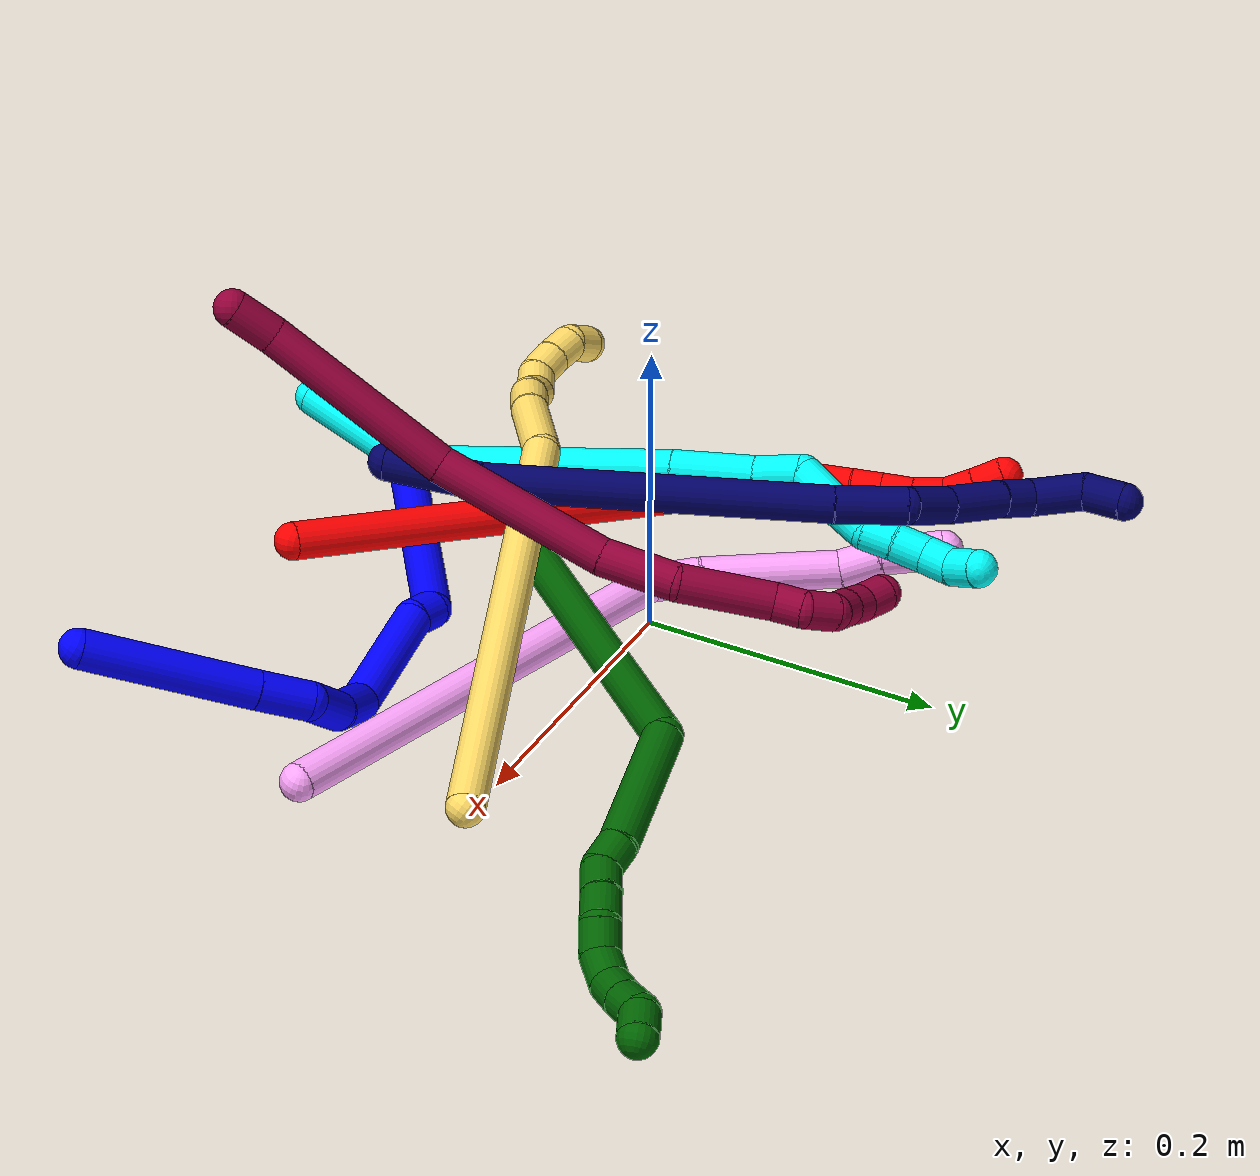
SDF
<sdf version="1.7">
 <world name="default">
  <plugin name="TubeGeneratorPlugin" filename="libtube_generator_plugin.so"/>
  <model name="photoneo_s_sensor">
   <static>1</static>
   <pose>0 0 2 1.57079 1.57079 3.14159</pose>
   <link name="link">
    <inertial><mass>0.1</mass></inertial>
    <sensor name="sensor" type="depth">
     <update_rate>30</update_rate>
     <camera>
      <horizontal_fov>1.22</horizontal_fov>
      <image><width>1920</width><height>1200</height><format>B8G8R8</format></image>
      <clip><near>0.1</near><far>4</far></clip>
      <depth_camera><output>points</output></depth_camera>
     </camera>
     <plugin name="camera_plugin" filename="libgazebo_ros_depth_camera.so">
      <baseline>0.2</baseline>
      <alwaysOn>1</alwaysOn>
      <updateRate>0.0</updateRate>
      <cameraName>camera_ir</cameraName>
      <imageTopicName>/camera/color/image_raw</imageTopicName>
      <cameraInfoTopicName>/camera/color/camera_info</cameraInfoTopicName>
      <depthImageTopicName>/camera/depth/image_raw</depthImageTopicName>
      <depthImageCameraInfoTopicName>/camera/depth/camera_info</depthImageCameraInfoTopicName>
      <pointCloudTopicName>/camera/depth/points</pointCloudTopicName>
      <frameName>fr_optical</frameName>
      <pointCloudCutoff>0.1</pointCloudCutoff>
      <pointCloudCutoffMax>2.0</pointCloudCutoffMax>
      <distortionK1>0</distortionK1>
      <distortionK2>0</distortionK2>
      <distortionK3>0</distortionK3>
      <distortionT1>0</distortionT1>
      <distortionT2>0</distortionT2>
      <CxPrime>0</CxPrime>
      <Cx>0</Cx>
      <Cy>0</Cy>
      <focalLength>0</focalLength>
      <hackBaseline>0</hackBaseline>
     </plugin>
    </sensor>
   </link>
  </model>
  <gravity>0 0 -9.8</gravity>
  <magnetic_field>6e-06 2.3e-05 -4.2e-05</magnetic_field>
  <atmosphere type="adiabatic"/>
  <physics name="default_physics" default="0" type="ode">
   <max_step_size>0.003</max_step_size>
   <real_time_factor>1</real_time_factor>
   <real_time_update_rate>1000</real_time_update_rate>
   <max_contacts>10000</max_contacts>
   <ode>
    <solver>
     <type>quick</type>
     <iters>100</iters>
     <sor>1.3</sor>
     <use_dynamic_moi_rescaling>0</use_dynamic_moi_rescaling>
    </solver>
    <constraints>
     <contact_max_correcting_vel>0</contact_max_correcting_vel>
     <contact_surface_layer>0.001</contact_surface_layer>
     <cfm>0</cfm>
     <erp>0.2</erp>
    </constraints>
   </ode>
  </physics>
  <scene><ambient>0.4 0.4 0.4 1</ambient><background>0.7 0.7 0.7 1</background><shadows>0</shadows></scene>
  <audio><device>default</device></audio>
  <spherical_coordinates>
   <surface_model>EARTH_WGS84</surface_model>
   <latitude_deg>0</latitude_deg>
   <longitude_deg>0</longitude_deg>
   <elevation>0</elevation>
   <heading_deg>0</heading_deg>
  </spherical_coordinates>
  <model name="bin">
   <static>1</static>
   <link name="bottom">
    <collision name="collision-bottom">
     <pose>0 0 -0.01 0 -0 0</pose>
     <geometry><box><size>0.8 0.6 0.02</size></box></geometry>
     <surface>
      <friction><ode><mu>100</mu><mu2>100</mu2></ode></friction>
      <contact><collide_bitmask>65535</collide_bitmask></contact>
     </surface>
    </collision>
   </link>
   <link name="west_wall">
    <collision name="collision-west_wall">
     <pose>-0.41 0 0.1 0 -0 0</pose>
     <geometry><box><size>0.02 0.6 0.2</size></box></geometry>
     <surface>
      <friction><ode><mu>100</mu><mu2>100</mu2></ode></friction>
      <contact><collide_bitmask>65535</collide_bitmask></contact>
     </surface>
    </collision>
   </link>
   <link name="east_wall">
    <collision name="collision-east_wall">
     <pose>0.41 0 0.1 0 -0 0</pose>
     <geometry><box><size>0.02 0.6 0.2</size></box></geometry>
     <surface>
      <friction><ode><mu>100</mu><mu2>100</mu2></ode></friction>
      <contact><collide_bitmask>65535</collide_bitmask></contact>
     </surface>
    </collision>
   </link>
   <link name="south_wall">
    <collision name="collision-south_wall">
     <pose>0 -0.31 0.1 0 -0 0</pose>
     <geometry><box><size>0.8 0.02 0.2</size></box></geometry>
     <surface>
      <friction><ode><mu>100</mu><mu2>100</mu2></ode></friction>
      <contact><collide_bitmask>65535</collide_bitmask></contact>
     </surface>
    </collision>
   </link>
   <link name="north_wall">
    <collision name="collision-north_wall">
     <pose>0 0.31 0.1 0 -0 0</pose>
     <geometry><box><size>0.8 0.02 0.2</size></box></geometry>
     <surface>
      <friction><ode><mu>100</mu><mu2>100</mu2></ode></friction>
      <contact><collide_bitmask>65535</collide_bitmask></contact>
     </surface>
    </collision>
   </link>
  </model>
  <model name="1">
   <static>0</static>
   <link name="1">
    <collision name="collision-cylinder-e_1_1_4">
     <pose>-0.009358 0.008161 -0.054589 -2.9932 -0.167947 1.69475</pose>
     <geometry><cylinder><radius>0.0125</radius><length>0.111966</length></cylinder></geometry>
     <surface>
      <friction><ode><mu>1.16</mu><mu2>1.16</mu2><slip1>0</slip1><slip2>0</slip2></ode></friction>
      <contact><ode><kp>1e+06</kp><kd>1</kd><max_vel>0</max_vel><min_depth>0.001</min_depth></ode></contact>
     </surface>
    </collision>
    <visual name="visual-cylinder-e_1_1_4">
     <pose>-0.009358 0.008161 -0.054589 -2.9932 -0.167947 1.69475</pose>
     <geometry><cylinder><radius>0.0125</radius><length>0.111966</length></cylinder></geometry>
     <material><ambient>0 0 1 1</ambient></material>
    </visual>
    <collision name="collision-cylinder-e_2_4_5">
     <pose>-0.022154 0.018804 -0.125964 -2.99474 -0.199869 1.87576</pose>
     <geometry><cylinder><radius>0.0125</radius><length>0.034627</length></cylinder></geometry>
     <surface>
      <friction><ode><mu>1.16</mu><mu2>1.16</mu2><slip1>0</slip1><slip2>0</slip2></ode></friction>
      <contact><ode><kp>1e+06</kp><kd>1</kd><max_vel>0</max_vel><min_depth>0.001</min_depth></ode></contact>
     </surface>
    </collision>
    <visual name="visual-cylinder-e_2_4_5">
     <pose>-0.022154 0.018804 -0.125964 -2.99474 -0.199869 1.87576</pose>
     <geometry><cylinder><radius>0.0125</radius><length>0.034627</length></cylinder></geometry>
     <material><ambient>0 0 1 1</ambient></material>
    </visual>
    <collision name="collision-cylinder-e_3_5_6">
     <pose>-0.036985 0.013668 -0.155525 2.60381 -0.653663 -1.77648</pose>
     <geometry><cylinder><radius>0.0125</radius><length>0.037474</length></cylinder></geometry>
     <surface>
      <friction><ode><mu>1.16</mu><mu2>1.16</mu2><slip1>0</slip1><slip2>0</slip2></ode></friction>
      <contact><ode><kp>1e+06</kp><kd>1</kd><max_vel>0</max_vel><min_depth>0.001</min_depth></ode></contact>
     </surface>
    </collision>
    <visual name="visual-cylinder-e_3_5_6">
     <pose>-0.036985 0.013668 -0.155525 2.60381 -0.653663 -1.77648</pose>
     <geometry><cylinder><radius>0.0125</radius><length>0.037474</length></cylinder></geometry>
     <material><ambient>0 0 1 1</ambient></material>
    </visual>
    <collision name="collision-cylinder-e_4_6_7">
     <pose>-0.067382 -0.001504 -0.178488 2.50366 -0.982278 -2.03529</pose>
     <geometry><cylinder><radius>0.0125</radius><length>0.045693</length></cylinder></geometry>
     <surface>
      <friction><ode><mu>1.16</mu><mu2>1.16</mu2><slip1>0</slip1><slip2>0</slip2></ode></friction>
      <contact><ode><kp>1e+06</kp><kd>1</kd><max_vel>0</max_vel><min_depth>0.001</min_depth></ode></contact>
     </surface>
    </collision>
    <visual name="visual-cylinder-e_4_6_7">
     <pose>-0.067382 -0.001504 -0.178488 2.50366 -0.982278 -2.03529</pose>
     <geometry><cylinder><radius>0.0125</radius><length>0.045693</length></cylinder></geometry>
     <material><ambient>0 0 1 1</ambient></material>
    </visual>
    <collision name="collision-cylinder-e_5_7_8">
     <pose>-0.124909 0.000939 -0.198651 -2.35508 -1.21945 2.0697</pose>
     <geometry><cylinder><radius>0.0125</radius><length>0.082062</length></cylinder></geometry>
     <surface>
      <friction><ode><mu>1.16</mu><mu2>1.16</mu2><slip1>0</slip1><slip2>0</slip2></ode></friction>
      <contact><ode><kp>1e+06</kp><kd>1</kd><max_vel>0</max_vel><min_depth>0.001</min_depth></ode></contact>
     </surface>
    </collision>
    <visual name="visual-cylinder-e_5_7_8">
     <pose>-0.124909 0.000939 -0.198651 -2.35508 -1.21945 2.0697</pose>
     <geometry><cylinder><radius>0.0125</radius><length>0.082062</length></cylinder></geometry>
     <material><ambient>0 0 1 1</ambient></material>
    </visual>
    <collision name="collision-cylinder-e_6_8_9">
     <pose>-0.171632 0.01152 -0.214552 -3.04332 -0.942571 2.94918</pose>
     <geometry><cylinder><radius>0.0125</radius><length>0.020268</length></cylinder></geometry>
     <surface>
      <friction><ode><mu>1.16</mu><mu2>1.16</mu2><slip1>0</slip1><slip2>0</slip2></ode></friction>
      <contact><ode><kp>1e+06</kp><kd>1</kd><max_vel>0</max_vel><min_depth>0.001</min_depth></ode></contact>
     </surface>
    </collision>
    <visual name="visual-cylinder-e_6_8_9">
     <pose>-0.171632 0.01152 -0.214552 -3.04332 -0.942571 2.94918</pose>
     <geometry><cylinder><radius>0.0125</radius><length>0.020268</length></cylinder></geometry>
     <material><ambient>0 0 1 1</ambient></material>
    </visual>
    <collision name="collision-cylinder-e_7_9_2">
     <pose>-0.261955 -0.003874 -0.213483 1.15809 -1.3615 -0.973971</pose>
     <geometry><cylinder><radius>0.0125</radius><length>0.16791</length></cylinder></geometry>
     <surface>
      <friction><ode><mu>1.16</mu><mu2>1.16</mu2><slip1>0</slip1><slip2>0</slip2></ode></friction>
      <contact><ode><kp>1e+06</kp><kd>1</kd><max_vel>0</max_vel><min_depth>0.001</min_depth></ode></contact>
     </surface>
    </collision>
    <visual name="visual-cylinder-e_7_9_2">
     <pose>-0.261955 -0.003874 -0.213483 1.15809 -1.3615 -0.973971</pose>
     <geometry><cylinder><radius>0.0125</radius><length>0.16791</length></cylinder></geometry>
     <material><ambient>0 0 1 1</ambient></material>
    </visual>
    <collision name="collision-sphere-2">
     <pose>-0.344077 -0.019852 -0.206487 0 -0 0</pose>
     <geometry><sphere><radius>0.0125</radius></sphere></geometry>
     <surface>
      <friction><ode><mu>1.16</mu><mu2>1.16</mu2><slip1>0</slip1><slip2>0</slip2></ode></friction>
      <contact><ode><kp>1e+06</kp><kd>1</kd><max_vel>0</max_vel><min_depth>0.001</min_depth></ode></contact>
     </surface>
    </collision>
    <visual name="visual-sphere-2">
     <pose>-0.344077 -0.019852 -0.206487 0 -0 0</pose>
     <geometry><sphere><radius>0.0125</radius></sphere></geometry>
     <material><ambient>0 0 1 1</ambient></material>
    </visual>
    <collision name="collision-sphere-9">
     <pose>-0.179832 0.012105 -0.22048 0 -0 0</pose>
     <geometry><sphere><radius>0.0125</radius></sphere></geometry>
     <surface>
      <friction><ode><mu>1.16</mu><mu2>1.16</mu2><slip1>0</slip1><slip2>0</slip2></ode></friction>
      <contact><ode><kp>1e+06</kp><kd>1</kd><max_vel>0</max_vel><min_depth>0.001</min_depth></ode></contact>
     </surface>
    </collision>
    <visual name="visual-sphere-9">
     <pose>-0.179832 0.012105 -0.22048 0 -0 0</pose>
     <geometry><sphere><radius>0.0125</radius></sphere></geometry>
     <material><ambient>0 0 1 1</ambient></material>
    </visual>
    <collision name="collision-sphere-4">
     <pose>-0.018716 0.016322 -0.109178 0 -0 0</pose>
     <geometry><sphere><radius>0.0125</radius></sphere></geometry>
     <surface>
      <friction><ode><mu>1.16</mu><mu2>1.16</mu2><slip1>0</slip1><slip2>0</slip2></ode></friction>
      <contact><ode><kp>1e+06</kp><kd>1</kd><max_vel>0</max_vel><min_depth>0.001</min_depth></ode></contact>
     </surface>
    </collision>
    <visual name="visual-sphere-4">
     <pose>-0.018716 0.016322 -0.109178 0 -0 0</pose>
     <geometry><sphere><radius>0.0125</radius></sphere></geometry>
     <material><ambient>0 0 1 1</ambient></material>
    </visual>
    <collision name="collision-sphere-1">
     <geometry><sphere><radius>0.0125</radius></sphere></geometry>
     <surface>
      <friction><ode><mu>1.16</mu><mu2>1.16</mu2><slip1>0</slip1><slip2>0</slip2></ode></friction>
      <contact><ode><kp>1e+06</kp><kd>1</kd><max_vel>0</max_vel><min_depth>0.001</min_depth></ode></contact>
     </surface>
    </collision>
    <visual name="visual-sphere-1">
     <geometry><sphere><radius>0.0125</radius></sphere></geometry>
     <material><ambient>0 0 1 1</ambient></material>
    </visual>
    <collision name="collision-sphere-8">
     <pose>-0.163433 0.010936 -0.208625 0 -0 0</pose>
     <geometry><sphere><radius>0.0125</radius></sphere></geometry>
     <surface>
      <friction><ode><mu>1.16</mu><mu2>1.16</mu2><slip1>0</slip1><slip2>0</slip2></ode></friction>
      <contact><ode><kp>1e+06</kp><kd>1</kd><max_vel>0</max_vel><min_depth>0.001</min_depth></ode></contact>
     </surface>
    </collision>
    <visual name="visual-sphere-8">
     <pose>-0.163433 0.010936 -0.208625 0 -0 0</pose>
     <geometry><sphere><radius>0.0125</radius></sphere></geometry>
     <material><ambient>0 0 1 1</ambient></material>
    </visual>
    <collision name="collision-sphere-5">
     <pose>-0.025591 0.021287 -0.14275 0 -0 0</pose>
     <geometry><sphere><radius>0.0125</radius></sphere></geometry>
     <surface>
      <friction><ode><mu>1.16</mu><mu2>1.16</mu2><slip1>0</slip1><slip2>0</slip2></ode></friction>
      <contact><ode><kp>1e+06</kp><kd>1</kd><max_vel>0</max_vel><min_depth>0.001</min_depth></ode></contact>
     </surface>
    </collision>
    <visual name="visual-sphere-5">
     <pose>-0.025591 0.021287 -0.14275 0 -0 0</pose>
     <geometry><sphere><radius>0.0125</radius></sphere></geometry>
     <material><ambient>0 0 1 1</ambient></material>
    </visual>
    <collision name="collision-sphere-6">
     <pose>-0.048379 0.006049 -0.1683 0 -0 0</pose>
     <geometry><sphere><radius>0.0125</radius></sphere></geometry>
     <surface>
      <friction><ode><mu>1.16</mu><mu2>1.16</mu2><slip1>0</slip1><slip2>0</slip2></ode></friction>
      <contact><ode><kp>1e+06</kp><kd>1</kd><max_vel>0</max_vel><min_depth>0.001</min_depth></ode></contact>
     </surface>
    </collision>
    <visual name="visual-sphere-6">
     <pose>-0.048379 0.006049 -0.1683 0 -0 0</pose>
     <geometry><sphere><radius>0.0125</radius></sphere></geometry>
     <material><ambient>0 0 1 1</ambient></material>
    </visual>
    <collision name="collision-sphere-7">
     <pose>-0.086384 -0.009057 -0.188677 0 -0 0</pose>
     <geometry><sphere><radius>0.0125</radius></sphere></geometry>
     <surface>
      <friction><ode><mu>1.16</mu><mu2>1.16</mu2><slip1>0</slip1><slip2>0</slip2></ode></friction>
      <contact><ode><kp>1e+06</kp><kd>1</kd><max_vel>0</max_vel><min_depth>0.001</min_depth></ode></contact>
     </surface>
    </collision>
    <visual name="visual-sphere-7">
     <pose>-0.086384 -0.009057 -0.188677 0 -0 0</pose>
     <geometry><sphere><radius>0.0125</radius></sphere></geometry>
     <material><ambient>0 0 1 1</ambient></material>
    </visual>
    <inertial>
     <pose>-0.127987 0.003337 -0.161908 0 -0 0</pose>
     <mass>0.5</mass>
     <inertia>
      <ixx>5.1e-05</ixx>
      <ixy>0</ixy>
      <ixz>0</ixz>
      <iyy>0.000523</iyy>
      <iyz>0</iyz>
      <izz>0.000508</izz>
     </inertia>
    </inertial>
   </link>
   <pose>0.330122 -0.209159 0.112748 1.01171 0.072037 0.451867</pose>
  </model>
  <model name="2">
   <static>0</static>
   <link name="2">
    <collision name="collision-cylinder-e_1_1_4">
     <pose>-0.105956 0.101033 -0.103489 -2.3682 -0.632273 1.35352</pose>
     <geometry><cylinder><radius>0.0125</radius><length>0.358577</length></cylinder></geometry>
     <surface>
      <friction><ode><mu>1.16</mu><mu2>1.16</mu2><slip1>0</slip1><slip2>0</slip2></ode></friction>
      <contact><ode><kp>1e+06</kp><kd>1</kd><max_vel>0</max_vel><min_depth>0.001</min_depth></ode></contact>
     </surface>
    </collision>
    <visual name="visual-cylinder-e_1_1_4">
     <pose>-0.105956 0.101033 -0.103489 -2.3682 -0.632273 1.35352</pose>
     <geometry><cylinder><radius>0.0125</radius><length>0.358577</length></cylinder></geometry>
     <material><ambient>1 0 0 1</ambient></material>
    </visual>
    <collision name="collision-cylinder-e_2_4_5">
     <pose>-0.214837 0.205579 -0.22439 -2.9425 -0.163216 1.37234</pose>
     <geometry><cylinder><radius>0.0125</radius><length>0.036004</length></cylinder></geometry>
     <surface>
      <friction><ode><mu>1.16</mu><mu2>1.16</mu2><slip1>0</slip1><slip2>0</slip2></ode></friction>
      <contact><ode><kp>1e+06</kp><kd>1</kd><max_vel>0</max_vel><min_depth>0.001</min_depth></ode></contact>
     </surface>
    </collision>
    <visual name="visual-cylinder-e_2_4_5">
     <pose>-0.214837 0.205579 -0.22439 -2.9425 -0.163216 1.37234</pose>
     <geometry><cylinder><radius>0.0125</radius><length>0.036004</length></cylinder></geometry>
     <material><ambient>1 0 0 1</ambient></material>
    </visual>
    <collision name="collision-cylinder-e_3_5_6">
     <pose>-0.220353 0.211334 -0.251234 -2.90826 -0.261164 1.68439</pose>
     <geometry><cylinder><radius>0.0125</radius><length>0.02007</length></cylinder></geometry>
     <surface>
      <friction><ode><mu>1.16</mu><mu2>1.16</mu2><slip1>0</slip1><slip2>0</slip2></ode></friction>
      <contact><ode><kp>1e+06</kp><kd>1</kd><max_vel>0</max_vel><min_depth>0.001</min_depth></ode></contact>
     </surface>
    </collision>
    <visual name="visual-cylinder-e_3_5_6">
     <pose>-0.220353 0.211334 -0.251234 -2.90826 -0.261164 1.68439</pose>
     <geometry><cylinder><radius>0.0125</radius><length>0.02007</length></cylinder></geometry>
     <material><ambient>1 0 0 1</ambient></material>
    </visual>
    <collision name="collision-cylinder-e_4_6_7">
     <pose>-0.225809 0.215929 -0.270898 -2.91553 -0.266358 1.73575</pose>
     <geometry><cylinder><radius>0.0125</radius><length>0.021766</length></cylinder></geometry>
     <surface>
      <friction><ode><mu>1.16</mu><mu2>1.16</mu2><slip1>0</slip1><slip2>0</slip2></ode></friction>
      <contact><ode><kp>1e+06</kp><kd>1</kd><max_vel>0</max_vel><min_depth>0.001</min_depth></ode></contact>
     </surface>
    </collision>
    <visual name="visual-cylinder-e_4_6_7">
     <pose>-0.225809 0.215929 -0.270898 -2.91553 -0.266358 1.73575</pose>
     <geometry><cylinder><radius>0.0125</radius><length>0.021766</length></cylinder></geometry>
     <material><ambient>1 0 0 1</ambient></material>
    </visual>
    <collision name="collision-cylinder-e_5_7_8">
     <pose>-0.230311 0.222014 -0.291518 -2.79666 -0.147308 0.801338</pose>
     <geometry><cylinder><radius>0.0125</radius><length>0.022317</length></cylinder></geometry>
     <surface>
      <friction><ode><mu>1.16</mu><mu2>1.16</mu2><slip1>0</slip1><slip2>0</slip2></ode></friction>
      <contact><ode><kp>1e+06</kp><kd>1</kd><max_vel>0</max_vel><min_depth>0.001</min_depth></ode></contact>
     </surface>
    </collision>
    <visual name="visual-cylinder-e_5_7_8">
     <pose>-0.230311 0.222014 -0.291518 -2.79666 -0.147308 0.801338</pose>
     <geometry><cylinder><radius>0.0125</radius><length>0.022317</length></cylinder></geometry>
     <material><ambient>1 0 0 1</ambient></material>
    </visual>
    <collision name="collision-cylinder-e_6_8_9">
     <pose>-0.232116 0.232036 -0.310396 -2.50399 -0.015827 0.047943</pose>
     <geometry><cylinder><radius>0.0125</radius><length>0.021135</length></cylinder></geometry>
     <surface>
      <friction><ode><mu>1.16</mu><mu2>1.16</mu2><slip1>0</slip1><slip2>0</slip2></ode></friction>
      <contact><ode><kp>1e+06</kp><kd>1</kd><max_vel>0</max_vel><min_depth>0.001</min_depth></ode></contact>
     </surface>
    </collision>
    <visual name="visual-cylinder-e_6_8_9">
     <pose>-0.232116 0.232036 -0.310396 -2.50399 -0.015827 0.047943</pose>
     <geometry><cylinder><radius>0.0125</radius><length>0.021135</length></cylinder></geometry>
     <material><ambient>1 0 0 1</ambient></material>
    </visual>
    <collision name="collision-cylinder-e_7_9_2">
     <pose>-0.232449 0.24476 -0.326625 -2.44806 -0.016413 0.045412</pose>
     <geometry><cylinder><radius>0.0125</radius><length>0.020131</length></cylinder></geometry>
     <surface>
      <friction><ode><mu>1.16</mu><mu2>1.16</mu2><slip1>0</slip1><slip2>0</slip2></ode></friction>
      <contact><ode><kp>1e+06</kp><kd>1</kd><max_vel>0</max_vel><min_depth>0.001</min_depth></ode></contact>
     </surface>
    </collision>
    <visual name="visual-cylinder-e_7_9_2">
     <pose>-0.232449 0.24476 -0.326625 -2.44806 -0.016413 0.045412</pose>
     <geometry><cylinder><radius>0.0125</radius><length>0.020131</length></cylinder></geometry>
     <material><ambient>1 0 0 1</ambient></material>
    </visual>
    <collision name="collision-sphere-2">
     <pose>-0.232614 0.251193 -0.334365 0 -0 0</pose>
     <geometry><sphere><radius>0.0125</radius></sphere></geometry>
     <surface>
      <friction><ode><mu>1.16</mu><mu2>1.16</mu2><slip1>0</slip1><slip2>0</slip2></ode></friction>
      <contact><ode><kp>1e+06</kp><kd>1</kd><max_vel>0</max_vel><min_depth>0.001</min_depth></ode></contact>
     </surface>
    </collision>
    <visual name="visual-sphere-2">
     <pose>-0.232614 0.251193 -0.334365 0 -0 0</pose>
     <geometry><sphere><radius>0.0125</radius></sphere></geometry>
     <material><ambient>1 0 0 1</ambient></material>
    </visual>
    <collision name="collision-sphere-9">
     <pose>-0.232284 0.238326 -0.318886 0 -0 0</pose>
     <geometry><sphere><radius>0.0125</radius></sphere></geometry>
     <surface>
      <friction><ode><mu>1.16</mu><mu2>1.16</mu2><slip1>0</slip1><slip2>0</slip2></ode></friction>
      <contact><ode><kp>1e+06</kp><kd>1</kd><max_vel>0</max_vel><min_depth>0.001</min_depth></ode></contact>
     </surface>
    </collision>
    <visual name="visual-sphere-9">
     <pose>-0.232284 0.238326 -0.318886 0 -0 0</pose>
     <geometry><sphere><radius>0.0125</radius></sphere></geometry>
     <material><ambient>1 0 0 1</ambient></material>
    </visual>
    <collision name="collision-sphere-4">
     <pose>-0.211912 0.202066 -0.206979 0 -0 0</pose>
     <geometry><sphere><radius>0.0125</radius></sphere></geometry>
     <surface>
      <friction><ode><mu>1.16</mu><mu2>1.16</mu2><slip1>0</slip1><slip2>0</slip2></ode></friction>
      <contact><ode><kp>1e+06</kp><kd>1</kd><max_vel>0</max_vel><min_depth>0.001</min_depth></ode></contact>
     </surface>
    </collision>
    <visual name="visual-sphere-4">
     <pose>-0.211912 0.202066 -0.206979 0 -0 0</pose>
     <geometry><sphere><radius>0.0125</radius></sphere></geometry>
     <material><ambient>1 0 0 1</ambient></material>
    </visual>
    <collision name="collision-sphere-1">
     <geometry><sphere><radius>0.0125</radius></sphere></geometry>
     <surface>
      <friction><ode><mu>1.16</mu><mu2>1.16</mu2><slip1>0</slip1><slip2>0</slip2></ode></friction>
      <contact><ode><kp>1e+06</kp><kd>1</kd><max_vel>0</max_vel><min_depth>0.001</min_depth></ode></contact>
     </surface>
    </collision>
    <visual name="visual-sphere-1">
     <geometry><sphere><radius>0.0125</radius></sphere></geometry>
     <material><ambient>1 0 0 1</ambient></material>
    </visual>
    <collision name="collision-sphere-8">
     <pose>-0.231949 0.225746 -0.301905 0 -0 0</pose>
     <geometry><sphere><radius>0.0125</radius></sphere></geometry>
     <surface>
      <friction><ode><mu>1.16</mu><mu2>1.16</mu2><slip1>0</slip1><slip2>0</slip2></ode></friction>
      <contact><ode><kp>1e+06</kp><kd>1</kd><max_vel>0</max_vel><min_depth>0.001</min_depth></ode></contact>
     </surface>
    </collision>
    <visual name="visual-sphere-8">
     <pose>-0.231949 0.225746 -0.301905 0 -0 0</pose>
     <geometry><sphere><radius>0.0125</radius></sphere></geometry>
     <material><ambient>1 0 0 1</ambient></material>
    </visual>
    <collision name="collision-sphere-5">
     <pose>-0.217762 0.209092 -0.241802 0 -0 0</pose>
     <geometry><sphere><radius>0.0125</radius></sphere></geometry>
     <surface>
      <friction><ode><mu>1.16</mu><mu2>1.16</mu2><slip1>0</slip1><slip2>0</slip2></ode></friction>
      <contact><ode><kp>1e+06</kp><kd>1</kd><max_vel>0</max_vel><min_depth>0.001</min_depth></ode></contact>
     </surface>
    </collision>
    <visual name="visual-sphere-5">
     <pose>-0.217762 0.209092 -0.241802 0 -0 0</pose>
     <geometry><sphere><radius>0.0125</radius></sphere></geometry>
     <material><ambient>1 0 0 1</ambient></material>
    </visual>
    <collision name="collision-sphere-6">
     <pose>-0.222944 0.213575 -0.260666 0 -0 0</pose>
     <geometry><sphere><radius>0.0125</radius></sphere></geometry>
     <surface>
      <friction><ode><mu>1.16</mu><mu2>1.16</mu2><slip1>0</slip1><slip2>0</slip2></ode></friction>
      <contact><ode><kp>1e+06</kp><kd>1</kd><max_vel>0</max_vel><min_depth>0.001</min_depth></ode></contact>
     </surface>
    </collision>
    <visual name="visual-sphere-6">
     <pose>-0.222944 0.213575 -0.260666 0 -0 0</pose>
     <geometry><sphere><radius>0.0125</radius></sphere></geometry>
     <material><ambient>1 0 0 1</ambient></material>
    </visual>
    <collision name="collision-sphere-7">
     <pose>-0.228673 0.218282 -0.281131 0 -0 0</pose>
     <geometry><sphere><radius>0.0125</radius></sphere></geometry>
     <surface>
      <friction><ode><mu>1.16</mu><mu2>1.16</mu2><slip1>0</slip1><slip2>0</slip2></ode></friction>
      <contact><ode><kp>1e+06</kp><kd>1</kd><max_vel>0</max_vel><min_depth>0.001</min_depth></ode></contact>
     </surface>
    </collision>
    <visual name="visual-sphere-7">
     <pose>-0.228673 0.218282 -0.281131 0 -0 0</pose>
     <geometry><sphere><radius>0.0125</radius></sphere></geometry>
     <material><ambient>1 0 0 1</ambient></material>
    </visual>
    <inertial>
     <pose>-0.139582 0.134714 -0.151536 0 -0 0</pose>
     <mass>0.5</mass>
     <inertia>
      <ixx>0.003704</ixx>
      <ixy>0</ixy>
      <ixz>0</ixz>
      <iyy>0.004023</iyy>
      <iyz>0</iyz>
      <izz>7.8e-05</izz>
     </inertia>
    </inertial>
   </link>
   <pose>0.09243 -0.210574 0.05069 1.63882 -0.922378 -0.121097</pose>
  </model>
  <model name="3">
   <static>0</static>
   <link name="3">
    <collision name="collision-cylinder-e_1_1_4">
     <pose>-0.007428 0.038695 0.022287 -1.04824 -0.164834 0.095426</pose>
     <geometry><cylinder><radius>0.0125</radius><length>0.090535</length></cylinder></geometry>
     <surface>
      <friction><ode><mu>1.16</mu><mu2>1.16</mu2><slip1>0</slip1><slip2>0</slip2></ode></friction>
      <contact><ode><kp>1e+06</kp><kd>1</kd><max_vel>0</max_vel><min_depth>0.001</min_depth></ode></contact>
     </surface>
    </collision>
    <visual name="visual-cylinder-e_1_1_4">
     <pose>-0.007428 0.038695 0.022287 -1.04824 -0.164834 0.095426</pose>
     <geometry><cylinder><radius>0.0125</radius><length>0.090535</length></cylinder></geometry>
     <material><ambient>0.003922 1 0.996078 1</ambient></material>
    </visual>
    <collision name="collision-cylinder-e_2_4_5">
     <pose>-0.06705 0.14703 0.05719 -1.39156 -0.63544 0.536049</pose>
     <geometry><cylinder><radius>0.0125</radius><length>0.175878</length></cylinder></geometry>
     <surface>
      <friction><ode><mu>1.16</mu><mu2>1.16</mu2><slip1>0</slip1><slip2>0</slip2></ode></friction>
      <contact><ode><kp>1e+06</kp><kd>1</kd><max_vel>0</max_vel><min_depth>0.001</min_depth></ode></contact>
     </surface>
    </collision>
    <visual name="visual-cylinder-e_2_4_5">
     <pose>-0.06705 0.14703 0.05719 -1.39156 -0.63544 0.536049</pose>
     <geometry><cylinder><radius>0.0125</radius><length>0.175878</length></cylinder></geometry>
     <material><ambient>0.003922 1 0.996078 1</ambient></material>
    </visual>
    <collision name="collision-cylinder-e_3_5_6">
     <pose>-0.134782 0.239527 0.074822 -1.35485 -0.586134 0.476262</pose>
     <geometry><cylinder><radius>0.0125</radius><length>0.056177</length></cylinder></geometry>
     <surface>
      <friction><ode><mu>1.16</mu><mu2>1.16</mu2><slip1>0</slip1><slip2>0</slip2></ode></friction>
      <contact><ode><kp>1e+06</kp><kd>1</kd><max_vel>0</max_vel><min_depth>0.001</min_depth></ode></contact>
     </surface>
    </collision>
    <visual name="visual-cylinder-e_3_5_6">
     <pose>-0.134782 0.239527 0.074822 -1.35485 -0.586134 0.476262</pose>
     <geometry><cylinder><radius>0.0125</radius><length>0.056177</length></cylinder></geometry>
     <material><ambient>0.003922 1 0.996078 1</ambient></material>
    </visual>
    <collision name="collision-cylinder-e_4_6_7">
     <pose>-0.160645 0.273797 0.083875 -1.23059 -0.706157 0.509636</pose>
     <geometry><cylinder><radius>0.0125</radius><length>0.031825</length></cylinder></geometry>
     <surface>
      <friction><ode><mu>1.16</mu><mu2>1.16</mu2><slip1>0</slip1><slip2>0</slip2></ode></friction>
      <contact><ode><kp>1e+06</kp><kd>1</kd><max_vel>0</max_vel><min_depth>0.001</min_depth></ode></contact>
     </surface>
    </collision>
    <visual name="visual-cylinder-e_4_6_7">
     <pose>-0.160645 0.273797 0.083875 -1.23059 -0.706157 0.509636</pose>
     <geometry><cylinder><radius>0.0125</radius><length>0.031825</length></cylinder></geometry>
     <material><ambient>0.003922 1 0.996078 1</ambient></material>
    </visual>
    <collision name="collision-cylinder-e_5_7_8">
     <pose>-0.170985 0.30006 0.098774 -0.939409 -0.00076 0.000386</pose>
     <geometry><cylinder><radius>0.0125</radius><length>0.036792</length></cylinder></geometry>
     <surface>
      <friction><ode><mu>1.16</mu><mu2>1.16</mu2><slip1>0</slip1><slip2>0</slip2></ode></friction>
      <contact><ode><kp>1e+06</kp><kd>1</kd><max_vel>0</max_vel><min_depth>0.001</min_depth></ode></contact>
     </surface>
    </collision>
    <visual name="visual-cylinder-e_5_7_8">
     <pose>-0.170985 0.30006 0.098774 -0.939409 -0.00076 0.000386</pose>
     <geometry><cylinder><radius>0.0125</radius><length>0.036792</length></cylinder></geometry>
     <material><ambient>0.003922 1 0.996078 1</ambient></material>
    </visual>
    <collision name="collision-cylinder-e_6_8_9">
     <pose>-0.171348 0.324691 0.116018 -0.992436 -0.029901 0.016189</pose>
     <geometry><cylinder><radius>0.0125</radius><length>0.023374</length></cylinder></geometry>
     <surface>
      <friction><ode><mu>1.16</mu><mu2>1.16</mu2><slip1>0</slip1><slip2>0</slip2></ode></friction>
      <contact><ode><kp>1e+06</kp><kd>1</kd><max_vel>0</max_vel><min_depth>0.001</min_depth></ode></contact>
     </surface>
    </collision>
    <visual name="visual-cylinder-e_6_8_9">
     <pose>-0.171348 0.324691 0.116018 -0.992436 -0.029901 0.016189</pose>
     <geometry><cylinder><radius>0.0125</radius><length>0.023374</length></cylinder></geometry>
     <material><ambient>0.003922 1 0.996078 1</ambient></material>
    </visual>
    <collision name="collision-cylinder-e_7_9_10">
     <pose>-0.175128 0.343938 0.125511 -1.25363 -0.331617 0.241221</pose>
     <geometry><cylinder><radius>0.0125</radius><length>0.021073</length></cylinder></geometry>
     <surface>
      <friction><ode><mu>1.16</mu><mu2>1.16</mu2><slip1>0</slip1><slip2>0</slip2></ode></friction>
      <contact><ode><kp>1e+06</kp><kd>1</kd><max_vel>0</max_vel><min_depth>0.001</min_depth></ode></contact>
     </surface>
    </collision>
    <visual name="visual-cylinder-e_7_9_10">
     <pose>-0.175128 0.343938 0.125511 -1.25363 -0.331617 0.241221</pose>
     <geometry><cylinder><radius>0.0125</radius><length>0.021073</length></cylinder></geometry>
     <material><ambient>0.003922 1 0.996078 1</ambient></material>
    </visual>
    <collision name="collision-cylinder-e_8_10_11">
     <pose>-0.181498 0.363707 0.131159 -1.32906 -0.270271 0.212224</pose>
     <geometry><cylinder><radius>0.0125</radius><length>0.022024</length></cylinder></geometry>
     <surface>
      <friction><ode><mu>1.16</mu><mu2>1.16</mu2><slip1>0</slip1><slip2>0</slip2></ode></friction>
      <contact><ode><kp>1e+06</kp><kd>1</kd><max_vel>0</max_vel><min_depth>0.001</min_depth></ode></contact>
     </surface>
    </collision>
    <visual name="visual-cylinder-e_8_10_11">
     <pose>-0.181498 0.363707 0.131159 -1.32906 -0.270271 0.212224</pose>
     <geometry><cylinder><radius>0.0125</radius><length>0.022024</length></cylinder></geometry>
     <material><ambient>0.003922 1 0.996078 1</ambient></material>
    </visual>
    <collision name="collision-cylinder-e_9_11_12">
     <pose>-0.187829 0.382152 0.139687 -0.936641 -0.323717 0.164825</pose>
     <geometry><cylinder><radius>0.0125</radius><length>0.02132</length></cylinder></geometry>
     <surface>
      <friction><ode><mu>1.16</mu><mu2>1.16</mu2><slip1>0</slip1><slip2>0</slip2></ode></friction>
      <contact><ode><kp>1e+06</kp><kd>1</kd><max_vel>0</max_vel><min_depth>0.001</min_depth></ode></contact>
     </surface>
    </collision>
    <visual name="visual-cylinder-e_9_11_12">
     <pose>-0.187829 0.382152 0.139687 -0.936641 -0.323717 0.164825</pose>
     <geometry><cylinder><radius>0.0125</radius><length>0.02132</length></cylinder></geometry>
     <material><ambient>0.003922 1 0.996078 1</ambient></material>
    </visual>
    <collision name="collision-cylinder-e_10_12_2">
     <pose>-0.197319 0.395695 0.152301 -0.683987 -0.619748 0.226983</pose>
     <geometry><cylinder><radius>0.0125</radius><length>0.021003</length></cylinder></geometry>
     <surface>
      <friction><ode><mu>1.16</mu><mu2>1.16</mu2><slip1>0</slip1><slip2>0</slip2></ode></friction>
      <contact><ode><kp>1e+06</kp><kd>1</kd><max_vel>0</max_vel><min_depth>0.001</min_depth></ode></contact>
     </surface>
    </collision>
    <visual name="visual-cylinder-e_10_12_2">
     <pose>-0.197319 0.395695 0.152301 -0.683987 -0.619748 0.226983</pose>
     <geometry><cylinder><radius>0.0125</radius><length>0.021003</length></cylinder></geometry>
     <material><ambient>0.003922 1 0.996078 1</ambient></material>
    </visual>
    <collision name="collision-sphere-2">
     <pose>-0.203419 0.401097 0.158926 0 -0 0</pose>
     <geometry><sphere><radius>0.0125</radius></sphere></geometry>
     <surface>
      <friction><ode><mu>1.16</mu><mu2>1.16</mu2><slip1>0</slip1><slip2>0</slip2></ode></friction>
      <contact><ode><kp>1e+06</kp><kd>1</kd><max_vel>0</max_vel><min_depth>0.001</min_depth></ode></contact>
     </surface>
    </collision>
    <visual name="visual-sphere-2">
     <pose>-0.203419 0.401097 0.158926 0 -0 0</pose>
     <geometry><sphere><radius>0.0125</radius></sphere></geometry>
     <material><ambient>0.003922 1 0.996078 1</ambient></material>
    </visual>
    <collision name="collision-sphere-12">
     <pose>-0.19122 0.390293 0.145675 0 -0 0</pose>
     <geometry><sphere><radius>0.0125</radius></sphere></geometry>
     <surface>
      <friction><ode><mu>1.16</mu><mu2>1.16</mu2><slip1>0</slip1><slip2>0</slip2></ode></friction>
      <contact><ode><kp>1e+06</kp><kd>1</kd><max_vel>0</max_vel><min_depth>0.001</min_depth></ode></contact>
     </surface>
    </collision>
    <visual name="visual-sphere-12">
     <pose>-0.19122 0.390293 0.145675 0 -0 0</pose>
     <geometry><sphere><radius>0.0125</radius></sphere></geometry>
     <material><ambient>0.003922 1 0.996078 1</ambient></material>
    </visual>
    <collision name="collision-sphere-11">
     <pose>-0.184438 0.374011 0.133699 0 -0 0</pose>
     <geometry><sphere><radius>0.0125</radius></sphere></geometry>
     <surface>
      <friction><ode><mu>1.16</mu><mu2>1.16</mu2><slip1>0</slip1><slip2>0</slip2></ode></friction>
      <contact><ode><kp>1e+06</kp><kd>1</kd><max_vel>0</max_vel><min_depth>0.001</min_depth></ode></contact>
     </surface>
    </collision>
    <visual name="visual-sphere-11">
     <pose>-0.184438 0.374011 0.133699 0 -0 0</pose>
     <geometry><sphere><radius>0.0125</radius></sphere></geometry>
     <material><ambient>0.003922 1 0.996078 1</ambient></material>
    </visual>
    <collision name="collision-sphere-10">
     <pose>-0.178558 0.353404 0.128618 0 -0 0</pose>
     <geometry><sphere><radius>0.0125</radius></sphere></geometry>
     <surface>
      <friction><ode><mu>1.16</mu><mu2>1.16</mu2><slip1>0</slip1><slip2>0</slip2></ode></friction>
      <contact><ode><kp>1e+06</kp><kd>1</kd><max_vel>0</max_vel><min_depth>0.001</min_depth></ode></contact>
     </surface>
    </collision>
    <visual name="visual-sphere-10">
     <pose>-0.178558 0.353404 0.128618 0 -0 0</pose>
     <geometry><sphere><radius>0.0125</radius></sphere></geometry>
     <material><ambient>0.003922 1 0.996078 1</ambient></material>
    </visual>
    <collision name="collision-sphere-9">
     <pose>-0.171697 0.334473 0.122404 0 -0 0</pose>
     <geometry><sphere><radius>0.0125</radius></sphere></geometry>
     <surface>
      <friction><ode><mu>1.16</mu><mu2>1.16</mu2><slip1>0</slip1><slip2>0</slip2></ode></friction>
      <contact><ode><kp>1e+06</kp><kd>1</kd><max_vel>0</max_vel><min_depth>0.001</min_depth></ode></contact>
     </surface>
    </collision>
    <visual name="visual-sphere-9">
     <pose>-0.171697 0.334473 0.122404 0 -0 0</pose>
     <geometry><sphere><radius>0.0125</radius></sphere></geometry>
     <material><ambient>0.003922 1 0.996078 1</ambient></material>
    </visual>
    <collision name="collision-sphere-4">
     <pose>-0.014856 0.07739 0.044573 0 -0 0</pose>
     <geometry><sphere><radius>0.0125</radius></sphere></geometry>
     <surface>
      <friction><ode><mu>1.16</mu><mu2>1.16</mu2><slip1>0</slip1><slip2>0</slip2></ode></friction>
      <contact><ode><kp>1e+06</kp><kd>1</kd><max_vel>0</max_vel><min_depth>0.001</min_depth></ode></contact>
     </surface>
    </collision>
    <visual name="visual-sphere-4">
     <pose>-0.014856 0.07739 0.044573 0 -0 0</pose>
     <geometry><sphere><radius>0.0125</radius></sphere></geometry>
     <material><ambient>0.003922 1 0.996078 1</ambient></material>
    </visual>
    <collision name="collision-sphere-1">
     <geometry><sphere><radius>0.0125</radius></sphere></geometry>
     <surface>
      <friction><ode><mu>1.16</mu><mu2>1.16</mu2><slip1>0</slip1><slip2>0</slip2></ode></friction>
      <contact><ode><kp>1e+06</kp><kd>1</kd><max_vel>0</max_vel><min_depth>0.001</min_depth></ode></contact>
     </surface>
    </collision>
    <visual name="visual-sphere-1">
     <geometry><sphere><radius>0.0125</radius></sphere></geometry>
     <material><ambient>0.003922 1 0.996078 1</ambient></material>
    </visual>
    <collision name="collision-sphere-8">
     <pose>-0.170999 0.314909 0.109632 0 -0 0</pose>
     <geometry><sphere><radius>0.0125</radius></sphere></geometry>
     <surface>
      <friction><ode><mu>1.16</mu><mu2>1.16</mu2><slip1>0</slip1><slip2>0</slip2></ode></friction>
      <contact><ode><kp>1e+06</kp><kd>1</kd><max_vel>0</max_vel><min_depth>0.001</min_depth></ode></contact>
     </surface>
    </collision>
    <visual name="visual-sphere-8">
     <pose>-0.170999 0.314909 0.109632 0 -0 0</pose>
     <geometry><sphere><radius>0.0125</radius></sphere></geometry>
     <material><ambient>0.003922 1 0.996078 1</ambient></material>
    </visual>
    <collision name="collision-sphere-5">
     <pose>-0.119245 0.21667 0.069808 0 -0 0</pose>
     <geometry><sphere><radius>0.0125</radius></sphere></geometry>
     <surface>
      <friction><ode><mu>1.16</mu><mu2>1.16</mu2><slip1>0</slip1><slip2>0</slip2></ode></friction>
      <contact><ode><kp>1e+06</kp><kd>1</kd><max_vel>0</max_vel><min_depth>0.001</min_depth></ode></contact>
     </surface>
    </collision>
    <visual name="visual-sphere-5">
     <pose>-0.119245 0.21667 0.069808 0 -0 0</pose>
     <geometry><sphere><radius>0.0125</radius></sphere></geometry>
     <material><ambient>0.003922 1 0.996078 1</ambient></material>
    </visual>
    <collision name="collision-sphere-6">
     <pose>-0.150319 0.262384 0.079835 0 -0 0</pose>
     <geometry><sphere><radius>0.0125</radius></sphere></geometry>
     <surface>
      <friction><ode><mu>1.16</mu><mu2>1.16</mu2><slip1>0</slip1><slip2>0</slip2></ode></friction>
      <contact><ode><kp>1e+06</kp><kd>1</kd><max_vel>0</max_vel><min_depth>0.001</min_depth></ode></contact>
     </surface>
    </collision>
    <visual name="visual-sphere-6">
     <pose>-0.150319 0.262384 0.079835 0 -0 0</pose>
     <geometry><sphere><radius>0.0125</radius></sphere></geometry>
     <material><ambient>0.003922 1 0.996078 1</ambient></material>
    </visual>
    <collision name="collision-sphere-7">
     <pose>-0.170971 0.28521 0.087916 0 -0 0</pose>
     <geometry><sphere><radius>0.0125</radius></sphere></geometry>
     <surface>
      <friction><ode><mu>1.16</mu><mu2>1.16</mu2><slip1>0</slip1><slip2>0</slip2></ode></friction>
      <contact><ode><kp>1e+06</kp><kd>1</kd><max_vel>0</max_vel><min_depth>0.001</min_depth></ode></contact>
     </surface>
    </collision>
    <visual name="visual-sphere-7">
     <pose>-0.170971 0.28521 0.087916 0 -0 0</pose>
     <geometry><sphere><radius>0.0125</radius></sphere></geometry>
     <material><ambient>0.003922 1 0.996078 1</ambient></material>
    </visual>
    <inertial>
     <pose>-0.102563 0.203754 0.07401 0 -0 0</pose>
     <mass>0.5</mass>
     <inertia>
      <ixx>0.0006</ixx>
      <ixy>0</ixy>
      <ixz>0</ixz>
      <iyy>0.000495</iyy>
      <iyz>0</iyz>
      <izz>-0.000138</izz>
     </inertia>
    </inertial>
   </link>
   <pose>-0.059046 -0.28848 0.0546 -1.15369 0.955125 -0.797108</pose>
  </model>
  <model name="4">
   <static>0</static>
   <link name="4">
    <collision name="collision-cylinder-e_1_1_4">
     <pose>-0.142194 0.053579 0.007499 -1.43174 -1.20723 1.08037</pose>
     <geometry><cylinder><radius>0.0125</radius><length>0.304277</length></cylinder></geometry>
     <surface>
      <friction><ode><mu>1.16</mu><mu2>1.16</mu2><slip1>0</slip1><slip2>0</slip2></ode></friction>
      <contact><ode><kp>1e+06</kp><kd>1</kd><max_vel>0</max_vel><min_depth>0.001</min_depth></ode></contact>
     </surface>
    </collision>
    <visual name="visual-cylinder-e_1_1_4">
     <pose>-0.142194 0.053579 0.007499 -1.43174 -1.20723 1.08037</pose>
     <geometry><cylinder><radius>0.0125</radius><length>0.304277</length></cylinder></geometry>
     <material><ambient>1 0.65098 0.996078 1</ambient></material>
    </visual>
    <collision name="collision-cylinder-e_2_4_5">
     <pose>-0.293188 0.120252 0.019889 -1.21328 -0.561946 0.395317</pose>
     <geometry><cylinder><radius>0.0125</radius><length>0.033032</length></cylinder></geometry>
     <surface>
      <friction><ode><mu>1.16</mu><mu2>1.16</mu2><slip1>0</slip1><slip2>0</slip2></ode></friction>
      <contact><ode><kp>1e+06</kp><kd>1</kd><max_vel>0</max_vel><min_depth>0.001</min_depth></ode></contact>
     </surface>
    </collision>
    <visual name="visual-cylinder-e_2_4_5">
     <pose>-0.293188 0.120252 0.019889 -1.21328 -0.561946 0.395317</pose>
     <geometry><cylinder><radius>0.0125</radius><length>0.033032</length></cylinder></geometry>
     <material><ambient>1 0.65098 0.996078 1</ambient></material>
    </visual>
    <collision name="collision-cylinder-e_3_5_6">
     <pose>-0.326342 0.171804 0.033447 -1.34913 -0.553363 0.446607</pose>
     <geometry><cylinder><radius>0.0125</radius><length>0.092679</length></cylinder></geometry>
     <surface>
      <friction><ode><mu>1.16</mu><mu2>1.16</mu2><slip1>0</slip1><slip2>0</slip2></ode></friction>
      <contact><ode><kp>1e+06</kp><kd>1</kd><max_vel>0</max_vel><min_depth>0.001</min_depth></ode></contact>
     </surface>
    </collision>
    <visual name="visual-cylinder-e_3_5_6">
     <pose>-0.326342 0.171804 0.033447 -1.34913 -0.553363 0.446607</pose>
     <geometry><cylinder><radius>0.0125</radius><length>0.092679</length></cylinder></geometry>
     <material><ambient>1 0.65098 0.996078 1</ambient></material>
    </visual>
    <collision name="collision-cylinder-e_4_6_7">
     <pose>-0.355184 0.220983 0.05135 -0.859674 -0.307114 0.141668</pose>
     <geometry><cylinder><radius>0.0125</radius><length>0.029689</length></cylinder></geometry>
     <surface>
      <friction><ode><mu>1.16</mu><mu2>1.16</mu2><slip1>0</slip1><slip2>0</slip2></ode></friction>
      <contact><ode><kp>1e+06</kp><kd>1</kd><max_vel>0</max_vel><min_depth>0.001</min_depth></ode></contact>
     </surface>
    </collision>
    <visual name="visual-cylinder-e_4_6_7">
     <pose>-0.355184 0.220983 0.05135 -0.859674 -0.307114 0.141668</pose>
     <geometry><cylinder><radius>0.0125</radius><length>0.029689</length></cylinder></geometry>
     <material><ambient>1 0.65098 0.996078 1</ambient></material>
    </visual>
    <collision name="collision-cylinder-e_5_7_8">
     <pose>-0.363149 0.240262 0.064703 -1.1224 -0.35105 0.222056</pose>
     <geometry><cylinder><radius>0.0125</radius><length>0.020229</length></cylinder></geometry>
     <surface>
      <friction><ode><mu>1.16</mu><mu2>1.16</mu2><slip1>0</slip1><slip2>0</slip2></ode></friction>
      <contact><ode><kp>1e+06</kp><kd>1</kd><max_vel>0</max_vel><min_depth>0.001</min_depth></ode></contact>
     </surface>
    </collision>
    <visual name="visual-cylinder-e_5_7_8">
     <pose>-0.363149 0.240262 0.064703 -1.1224 -0.35105 0.222056</pose>
     <geometry><cylinder><radius>0.0125</radius><length>0.020229</length></cylinder></geometry>
     <material><ambient>1 0.65098 0.996078 1</ambient></material>
    </visual>
    <collision name="collision-cylinder-e_6_8_2">
     <pose>-0.370518 0.257131 0.072914 -1.11304 -0.397618 0.249373</pose>
     <geometry><cylinder><radius>0.0125</radius><length>0.020094</length></cylinder></geometry>
     <surface>
      <friction><ode><mu>1.16</mu><mu2>1.16</mu2><slip1>0</slip1><slip2>0</slip2></ode></friction>
      <contact><ode><kp>1e+06</kp><kd>1</kd><max_vel>0</max_vel><min_depth>0.001</min_depth></ode></contact>
     </surface>
    </collision>
    <visual name="visual-cylinder-e_6_8_2">
     <pose>-0.370518 0.257131 0.072914 -1.11304 -0.397618 0.249373</pose>
     <geometry><cylinder><radius>0.0125</radius><length>0.020094</length></cylinder></geometry>
     <material><ambient>1 0.65098 0.996078 1</ambient></material>
    </visual>
    <collision name="collision-sphere-2">
     <pose>-0.374409 0.26544 0.077008 0 -0 0</pose>
     <geometry><sphere><radius>0.0125</radius></sphere></geometry>
     <surface>
      <friction><ode><mu>1.16</mu><mu2>1.16</mu2><slip1>0</slip1><slip2>0</slip2></ode></friction>
      <contact><ode><kp>1e+06</kp><kd>1</kd><max_vel>0</max_vel><min_depth>0.001</min_depth></ode></contact>
     </surface>
    </collision>
    <visual name="visual-sphere-2">
     <pose>-0.374409 0.26544 0.077008 0 -0 0</pose>
     <geometry><sphere><radius>0.0125</radius></sphere></geometry>
     <material><ambient>1 0.65098 0.996078 1</ambient></material>
    </visual>
    <collision name="collision-sphere-4">
     <pose>-0.284388 0.107159 0.014998 0 -0 0</pose>
     <geometry><sphere><radius>0.0125</radius></sphere></geometry>
     <surface>
      <friction><ode><mu>1.16</mu><mu2>1.16</mu2><slip1>0</slip1><slip2>0</slip2></ode></friction>
      <contact><ode><kp>1e+06</kp><kd>1</kd><max_vel>0</max_vel><min_depth>0.001</min_depth></ode></contact>
     </surface>
    </collision>
    <visual name="visual-sphere-4">
     <pose>-0.284388 0.107159 0.014998 0 -0 0</pose>
     <geometry><sphere><radius>0.0125</radius></sphere></geometry>
     <material><ambient>1 0.65098 0.996078 1</ambient></material>
    </visual>
    <collision name="collision-sphere-1">
     <geometry><sphere><radius>0.0125</radius></sphere></geometry>
     <surface>
      <friction><ode><mu>1.16</mu><mu2>1.16</mu2><slip1>0</slip1><slip2>0</slip2></ode></friction>
      <contact><ode><kp>1e+06</kp><kd>1</kd><max_vel>0</max_vel><min_depth>0.001</min_depth></ode></contact>
     </surface>
    </collision>
    <visual name="visual-sphere-1">
     <geometry><sphere><radius>0.0125</radius></sphere></geometry>
     <material><ambient>1 0.65098 0.996078 1</ambient></material>
    </visual>
    <collision name="collision-sphere-8">
     <pose>-0.366628 0.248821 0.06882 0 -0 0</pose>
     <geometry><sphere><radius>0.0125</radius></sphere></geometry>
     <surface>
      <friction><ode><mu>1.16</mu><mu2>1.16</mu2><slip1>0</slip1><slip2>0</slip2></ode></friction>
      <contact><ode><kp>1e+06</kp><kd>1</kd><max_vel>0</max_vel><min_depth>0.001</min_depth></ode></contact>
     </surface>
    </collision>
    <visual name="visual-sphere-8">
     <pose>-0.366628 0.248821 0.06882 0 -0 0</pose>
     <geometry><sphere><radius>0.0125</radius></sphere></geometry>
     <material><ambient>1 0.65098 0.996078 1</ambient></material>
    </visual>
    <collision name="collision-sphere-5">
     <pose>-0.301988 0.133344 0.02478 0 -0 0</pose>
     <geometry><sphere><radius>0.0125</radius></sphere></geometry>
     <surface>
      <friction><ode><mu>1.16</mu><mu2>1.16</mu2><slip1>0</slip1><slip2>0</slip2></ode></friction>
      <contact><ode><kp>1e+06</kp><kd>1</kd><max_vel>0</max_vel><min_depth>0.001</min_depth></ode></contact>
     </surface>
    </collision>
    <visual name="visual-sphere-5">
     <pose>-0.301988 0.133344 0.02478 0 -0 0</pose>
     <geometry><sphere><radius>0.0125</radius></sphere></geometry>
     <material><ambient>1 0.65098 0.996078 1</ambient></material>
    </visual>
    <collision name="collision-sphere-6">
     <pose>-0.350696 0.210263 0.042115 0 -0 0</pose>
     <geometry><sphere><radius>0.0125</radius></sphere></geometry>
     <surface>
      <friction><ode><mu>1.16</mu><mu2>1.16</mu2><slip1>0</slip1><slip2>0</slip2></ode></friction>
      <contact><ode><kp>1e+06</kp><kd>1</kd><max_vel>0</max_vel><min_depth>0.001</min_depth></ode></contact>
     </surface>
    </collision>
    <visual name="visual-sphere-6">
     <pose>-0.350696 0.210263 0.042115 0 -0 0</pose>
     <geometry><sphere><radius>0.0125</radius></sphere></geometry>
     <material><ambient>1 0.65098 0.996078 1</ambient></material>
    </visual>
    <collision name="collision-sphere-7">
     <pose>-0.359671 0.231704 0.060585 0 -0 0</pose>
     <geometry><sphere><radius>0.0125</radius></sphere></geometry>
     <surface>
      <friction><ode><mu>1.16</mu><mu2>1.16</mu2><slip1>0</slip1><slip2>0</slip2></ode></friction>
      <contact><ode><kp>1e+06</kp><kd>1</kd><max_vel>0</max_vel><min_depth>0.001</min_depth></ode></contact>
     </surface>
    </collision>
    <visual name="visual-sphere-7">
     <pose>-0.359671 0.231704 0.060585 0 -0 0</pose>
     <geometry><sphere><radius>0.0125</radius></sphere></geometry>
     <material><ambient>1 0.65098 0.996078 1</ambient></material>
    </visual>
    <inertial>
     <pose>-0.217065 0.105571 0.020674 0 -0 0</pose>
     <mass>0.5</mass>
     <inertia>
      <ixx>0.001197</ixx>
      <ixy>0</ixy>
      <ixz>0</ixz>
      <iyy>0.002905</iyy>
      <iyz>0</iyz>
      <izz>0.001355</izz>
     </inertia>
    </inertial>
   </link>
   <pose>0.265081 -0.100851 0.009911 -0.292366 0.058056 0.071445</pose>
  </model>
  <model name="5">
   <static>0</static>
   <link name="5">
    <collision name="collision-cylinder-e_1_1_4">
     <pose>-0.116917 -0.033711 0.104275 0.312686 -0.81774 -0.136386</pose>
     <geometry><cylinder><radius>0.0125</radius><length>0.320494</length></cylinder></geometry>
     <surface>
      <friction><ode><mu>1.16</mu><mu2>1.16</mu2><slip1>0</slip1><slip2>0</slip2></ode></friction>
      <contact><ode><kp>1e+06</kp><kd>1</kd><max_vel>0</max_vel><min_depth>0.001</min_depth></ode></contact>
     </surface>
    </collision>
    <visual name="visual-cylinder-e_1_1_4">
     <pose>-0.116917 -0.033711 0.104275 0.312686 -0.81774 -0.136386</pose>
     <geometry><cylinder><radius>0.0125</radius><length>0.320494</length></cylinder></geometry>
     <material><ambient>1 0.858824 0.4 1</ambient></material>
    </visual>
    <collision name="collision-cylinder-e_2_4_5">
     <pose>-0.256875 -0.076245 0.217775 0.763107 -1.06486 -0.464258</pose>
     <geometry><cylinder><radius>0.0125</radius><length>0.052683</length></cylinder></geometry>
     <surface>
      <friction><ode><mu>1.16</mu><mu2>1.16</mu2><slip1>0</slip1><slip2>0</slip2></ode></friction>
      <contact><ode><kp>1e+06</kp><kd>1</kd><max_vel>0</max_vel><min_depth>0.001</min_depth></ode></contact>
     </surface>
    </collision>
    <visual name="visual-cylinder-e_2_4_5">
     <pose>-0.256875 -0.076245 0.217775 0.763107 -1.06486 -0.464258</pose>
     <geometry><cylinder><radius>0.0125</radius><length>0.052683</length></cylinder></geometry>
     <material><ambient>1 0.858824 0.4 1</ambient></material>
    </visual>
    <collision name="collision-cylinder-e_3_5_6">
     <pose>-0.290431 -0.087263 0.231404 0.462209 -1.13318 -0.297186</pose>
     <geometry><cylinder><radius>0.0125</radius><length>0.023217</length></cylinder></geometry>
     <surface>
      <friction><ode><mu>1.16</mu><mu2>1.16</mu2><slip1>0</slip1><slip2>0</slip2></ode></friction>
      <contact><ode><kp>1e+06</kp><kd>1</kd><max_vel>0</max_vel><min_depth>0.001</min_depth></ode></contact>
     </surface>
    </collision>
    <visual name="visual-cylinder-e_3_5_6">
     <pose>-0.290431 -0.087263 0.231404 0.462209 -1.13318 -0.297186</pose>
     <geometry><cylinder><radius>0.0125</radius><length>0.023217</length></cylinder></geometry>
     <material><ambient>1 0.858824 0.4 1</ambient></material>
    </visual>
    <collision name="collision-cylinder-e_4_6_7">
     <pose>-0.31044 -0.087231 0.23807 -0.777038 -1.24814 0.573255</pose>
     <geometry><cylinder><radius>0.0125</radius><length>0.020022</length></cylinder></geometry>
     <surface>
      <friction><ode><mu>1.16</mu><mu2>1.16</mu2><slip1>0</slip1><slip2>0</slip2></ode></friction>
      <contact><ode><kp>1e+06</kp><kd>1</kd><max_vel>0</max_vel><min_depth>0.001</min_depth></ode></contact>
     </surface>
    </collision>
    <visual name="visual-cylinder-e_4_6_7">
     <pose>-0.31044 -0.087231 0.23807 -0.777038 -1.24814 0.573255</pose>
     <geometry><cylinder><radius>0.0125</radius><length>0.020022</length></cylinder></geometry>
     <material><ambient>1 0.858824 0.4 1</ambient></material>
    </visual>
    <collision name="collision-cylinder-e_5_7_8">
     <pose>-0.328664 -0.087655 0.245825 0.449649 -0.961066 -0.237308</pose>
     <geometry><cylinder><radius>0.0125</radius><length>0.021295</length></cylinder></geometry>
     <surface>
      <friction><ode><mu>1.16</mu><mu2>1.16</mu2><slip1>0</slip1><slip2>0</slip2></ode></friction>
      <contact><ode><kp>1e+06</kp><kd>1</kd><max_vel>0</max_vel><min_depth>0.001</min_depth></ode></contact>
     </surface>
    </collision>
    <visual name="visual-cylinder-e_5_7_8">
     <pose>-0.328664 -0.087655 0.245825 0.449649 -0.961066 -0.237308</pose>
     <geometry><cylinder><radius>0.0125</radius><length>0.021295</length></cylinder></geometry>
     <material><ambient>1 0.858824 0.4 1</ambient></material>
    </visual>
    <collision name="collision-cylinder-e_6_8_9">
     <pose>-0.34377 -0.08889 0.259651 -0.168134 -0.646307 0.056425</pose>
     <geometry><cylinder><radius>0.0125</radius><length>0.02118</length></cylinder></geometry>
     <surface>
      <friction><ode><mu>1.16</mu><mu2>1.16</mu2><slip1>0</slip1><slip2>0</slip2></ode></friction>
      <contact><ode><kp>1e+06</kp><kd>1</kd><max_vel>0</max_vel><min_depth>0.001</min_depth></ode></contact>
     </surface>
    </collision>
    <visual name="visual-cylinder-e_6_8_9">
     <pose>-0.34377 -0.08889 0.259651 -0.168134 -0.646307 0.056425</pose>
     <geometry><cylinder><radius>0.0125</radius><length>0.02118</length></cylinder></geometry>
     <material><ambient>1 0.858824 0.4 1</ambient></material>
    </visual>
    <collision name="collision-cylinder-e_7_9_10">
     <pose>-0.35599 -0.085091 0.275897 -0.292792 -0.61539 0.093648</pose>
     <geometry><cylinder><radius>0.0125</radius><length>0.020239</length></cylinder></geometry>
     <surface>
      <friction><ode><mu>1.16</mu><mu2>1.16</mu2><slip1>0</slip1><slip2>0</slip2></ode></friction>
      <contact><ode><kp>1e+06</kp><kd>1</kd><max_vel>0</max_vel><min_depth>0.001</min_depth></ode></contact>
     </surface>
    </collision>
    <visual name="visual-cylinder-e_7_9_10">
     <pose>-0.35599 -0.085091 0.275897 -0.292792 -0.61539 0.093648</pose>
     <geometry><cylinder><radius>0.0125</radius><length>0.020239</length></cylinder></geometry>
     <material><ambient>1 0.858824 0.4 1</ambient></material>
    </visual>
    <collision name="collision-cylinder-e_8_10_2">
     <pose>-0.369791 -0.077027 0.287453 -1.00026 -0.867642 0.495894</pose>
     <geometry><cylinder><radius>0.0125</radius><length>0.020869</length></cylinder></geometry>
     <surface>
      <friction><ode><mu>1.16</mu><mu2>1.16</mu2><slip1>0</slip1><slip2>0</slip2></ode></friction>
      <contact><ode><kp>1e+06</kp><kd>1</kd><max_vel>0</max_vel><min_depth>0.001</min_depth></ode></contact>
     </surface>
    </collision>
    <visual name="visual-cylinder-e_8_10_2">
     <pose>-0.369791 -0.077027 0.287453 -1.00026 -0.867642 0.495894</pose>
     <geometry><cylinder><radius>0.0125</radius><length>0.020869</length></cylinder></geometry>
     <material><ambient>1 0.858824 0.4 1</ambient></material>
    </visual>
    <collision name="collision-sphere-2">
     <pose>-0.377751 -0.071348 0.291097 0 -0 0</pose>
     <geometry><sphere><radius>0.0125</radius></sphere></geometry>
     <surface>
      <friction><ode><mu>1.16</mu><mu2>1.16</mu2><slip1>0</slip1><slip2>0</slip2></ode></friction>
      <contact><ode><kp>1e+06</kp><kd>1</kd><max_vel>0</max_vel><min_depth>0.001</min_depth></ode></contact>
     </surface>
    </collision>
    <visual name="visual-sphere-2">
     <pose>-0.377751 -0.071348 0.291097 0 -0 0</pose>
     <geometry><sphere><radius>0.0125</radius></sphere></geometry>
     <material><ambient>1 0.858824 0.4 1</ambient></material>
    </visual>
    <collision name="collision-sphere-10">
     <pose>-0.361832 -0.082706 0.283809 0 -0 0</pose>
     <geometry><sphere><radius>0.0125</radius></sphere></geometry>
     <surface>
      <friction><ode><mu>1.16</mu><mu2>1.16</mu2><slip1>0</slip1><slip2>0</slip2></ode></friction>
      <contact><ode><kp>1e+06</kp><kd>1</kd><max_vel>0</max_vel><min_depth>0.001</min_depth></ode></contact>
     </surface>
    </collision>
    <visual name="visual-sphere-10">
     <pose>-0.361832 -0.082706 0.283809 0 -0 0</pose>
     <geometry><sphere><radius>0.0125</radius></sphere></geometry>
     <material><ambient>1 0.858824 0.4 1</ambient></material>
    </visual>
    <collision name="collision-sphere-9">
     <pose>-0.350148 -0.087475 0.267986 0 -0 0</pose>
     <geometry><sphere><radius>0.0125</radius></sphere></geometry>
     <surface>
      <friction><ode><mu>1.16</mu><mu2>1.16</mu2><slip1>0</slip1><slip2>0</slip2></ode></friction>
      <contact><ode><kp>1e+06</kp><kd>1</kd><max_vel>0</max_vel><min_depth>0.001</min_depth></ode></contact>
     </surface>
    </collision>
    <visual name="visual-sphere-9">
     <pose>-0.350148 -0.087475 0.267986 0 -0 0</pose>
     <geometry><sphere><radius>0.0125</radius></sphere></geometry>
     <material><ambient>1 0.858824 0.4 1</ambient></material>
    </visual>
    <collision name="collision-sphere-4">
     <pose>-0.233833 -0.067422 0.208549 0 -0 0</pose>
     <geometry><sphere><radius>0.0125</radius></sphere></geometry>
     <surface>
      <friction><ode><mu>1.16</mu><mu2>1.16</mu2><slip1>0</slip1><slip2>0</slip2></ode></friction>
      <contact><ode><kp>1e+06</kp><kd>1</kd><max_vel>0</max_vel><min_depth>0.001</min_depth></ode></contact>
     </surface>
    </collision>
    <visual name="visual-sphere-4">
     <pose>-0.233833 -0.067422 0.208549 0 -0 0</pose>
     <geometry><sphere><radius>0.0125</radius></sphere></geometry>
     <material><ambient>1 0.858824 0.4 1</ambient></material>
    </visual>
    <collision name="collision-sphere-1">
     <geometry><sphere><radius>0.0125</radius></sphere></geometry>
     <surface>
      <friction><ode><mu>1.16</mu><mu2>1.16</mu2><slip1>0</slip1><slip2>0</slip2></ode></friction>
      <contact><ode><kp>1e+06</kp><kd>1</kd><max_vel>0</max_vel><min_depth>0.001</min_depth></ode></contact>
     </surface>
    </collision>
    <visual name="visual-sphere-1">
     <geometry><sphere><radius>0.0125</radius></sphere></geometry>
     <material><ambient>1 0.858824 0.4 1</ambient></material>
    </visual>
    <collision name="collision-sphere-8">
     <pose>-0.337392 -0.090305 0.251316 0 -0 0</pose>
     <geometry><sphere><radius>0.0125</radius></sphere></geometry>
     <surface>
      <friction><ode><mu>1.16</mu><mu2>1.16</mu2><slip1>0</slip1><slip2>0</slip2></ode></friction>
      <contact><ode><kp>1e+06</kp><kd>1</kd><max_vel>0</max_vel><min_depth>0.001</min_depth></ode></contact>
     </surface>
    </collision>
    <visual name="visual-sphere-8">
     <pose>-0.337392 -0.090305 0.251316 0 -0 0</pose>
     <geometry><sphere><radius>0.0125</radius></sphere></geometry>
     <material><ambient>1 0.858824 0.4 1</ambient></material>
    </visual>
    <collision name="collision-sphere-5">
     <pose>-0.279916 -0.085069 0.227001 0 -0 0</pose>
     <geometry><sphere><radius>0.0125</radius></sphere></geometry>
     <surface>
      <friction><ode><mu>1.16</mu><mu2>1.16</mu2><slip1>0</slip1><slip2>0</slip2></ode></friction>
      <contact><ode><kp>1e+06</kp><kd>1</kd><max_vel>0</max_vel><min_depth>0.001</min_depth></ode></contact>
     </surface>
    </collision>
    <visual name="visual-sphere-5">
     <pose>-0.279916 -0.085069 0.227001 0 -0 0</pose>
     <geometry><sphere><radius>0.0125</radius></sphere></geometry>
     <material><ambient>1 0.858824 0.4 1</ambient></material>
    </visual>
    <collision name="collision-sphere-6">
     <pose>-0.300946 -0.089456 0.235807 0 -0 0</pose>
     <geometry><sphere><radius>0.0125</radius></sphere></geometry>
     <surface>
      <friction><ode><mu>1.16</mu><mu2>1.16</mu2><slip1>0</slip1><slip2>0</slip2></ode></friction>
      <contact><ode><kp>1e+06</kp><kd>1</kd><max_vel>0</max_vel><min_depth>0.001</min_depth></ode></contact>
     </surface>
    </collision>
    <visual name="visual-sphere-6">
     <pose>-0.300946 -0.089456 0.235807 0 -0 0</pose>
     <geometry><sphere><radius>0.0125</radius></sphere></geometry>
     <material><ambient>1 0.858824 0.4 1</ambient></material>
    </visual>
    <collision name="collision-sphere-7">
     <pose>-0.319935 -0.085005 0.240334 0 -0 0</pose>
     <geometry><sphere><radius>0.0125</radius></sphere></geometry>
     <surface>
      <friction><ode><mu>1.16</mu><mu2>1.16</mu2><slip1>0</slip1><slip2>0</slip2></ode></friction>
      <contact><ode><kp>1e+06</kp><kd>1</kd><max_vel>0</max_vel><min_depth>0.001</min_depth></ode></contact>
     </surface>
    </collision>
    <visual name="visual-sphere-7">
     <pose>-0.319935 -0.085005 0.240334 0 -0 0</pose>
     <geometry><sphere><radius>0.0125</radius></sphere></geometry>
     <material><ambient>1 0.858824 0.4 1</ambient></material>
    </visual>
    <inertial>
     <pose>-0.18633 -0.051345 0.154698 0 -0 0</pose>
     <mass>0.5</mass>
     <inertia><ixx>0.00159</ixx><ixy>0</ixy><ixz>0</ixz><iyy>0.00244</iyy><iyz>0</iyz><izz>0.002637</izz></inertia>
    </inertial>
   </link>
   <pose>0.242315 0.002892 0.012231 -0.712016 -0.526718 0.636019</pose>
  </model>
  <model name="6">
   <static>0</static>
   <link name="6">
    <collision name="collision-cylinder-e_1_1_4">
     <pose>0.079461 0.060583 0.073463 -0.689604 0.69542 -0.258881</pose>
     <geometry><cylinder><radius>0.0125</radius><length>0.248041</length></cylinder></geometry>
     <surface>
      <friction><ode><mu>1.16</mu><mu2>1.16</mu2><slip1>0</slip1><slip2>0</slip2></ode></friction>
      <contact><ode><kp>1e+06</kp><kd>1</kd><max_vel>0</max_vel><min_depth>0.001</min_depth></ode></contact>
     </surface>
    </collision>
    <visual name="visual-cylinder-e_1_1_4">
     <pose>0.079461 0.060583 0.073463 -0.689604 0.69542 -0.258881</pose>
     <geometry><cylinder><radius>0.0125</radius><length>0.248041</length></cylinder></geometry>
     <material><ambient>0 0.392157 0.003922 1</ambient></material>
    </visual>
    <collision name="collision-cylinder-e_2_4_5">
     <pose>0.160401 0.141549 0.187621 -0.464354 0.032497 -0.007684</pose>
     <geometry><cylinder><radius>0.0125</radius><length>0.091079</length></cylinder></geometry>
     <surface>
      <friction><ode><mu>1.16</mu><mu2>1.16</mu2><slip1>0</slip1><slip2>0</slip2></ode></friction>
      <contact><ode><kp>1e+06</kp><kd>1</kd><max_vel>0</max_vel><min_depth>0.001</min_depth></ode></contact>
     </surface>
    </collision>
    <visual name="visual-cylinder-e_2_4_5">
     <pose>0.160401 0.141549 0.187621 -0.464354 0.032497 -0.007684</pose>
     <geometry><cylinder><radius>0.0125</radius><length>0.091079</length></cylinder></geometry>
     <material><ambient>0 0.392157 0.003922 1</ambient></material>
    </visual>
    <collision name="collision-cylinder-e_3_5_6">
     <pose>0.159988 0.166368 0.23738 -0.455052 -0.18547 0.04306</pose>
     <geometry><cylinder><radius>0.0125</radius><length>0.020532</length></cylinder></geometry>
     <surface>
      <friction><ode><mu>1.16</mu><mu2>1.16</mu2><slip1>0</slip1><slip2>0</slip2></ode></friction>
      <contact><ode><kp>1e+06</kp><kd>1</kd><max_vel>0</max_vel><min_depth>0.001</min_depth></ode></contact>
     </surface>
    </collision>
    <visual name="visual-cylinder-e_3_5_6">
     <pose>0.159988 0.166368 0.23738 -0.455052 -0.18547 0.04306</pose>
     <geometry><cylinder><radius>0.0125</radius><length>0.020532</length></cylinder></geometry>
     <material><ambient>0 0.392157 0.003922 1</ambient></material>
    </visual>
    <collision name="collision-cylinder-e_4_6_7">
     <pose>0.1614 0.174682 0.255103 -0.421242 0.33514 -0.072297</pose>
     <geometry><cylinder><radius>0.0125</radius><length>0.020096</length></cylinder></geometry>
     <surface>
      <friction><ode><mu>1.16</mu><mu2>1.16</mu2><slip1>0</slip1><slip2>0</slip2></ode></friction>
      <contact><ode><kp>1e+06</kp><kd>1</kd><max_vel>0</max_vel><min_depth>0.001</min_depth></ode></contact>
     </surface>
    </collision>
    <visual name="visual-cylinder-e_4_6_7">
     <pose>0.1614 0.174682 0.255103 -0.421242 0.33514 -0.072297</pose>
     <geometry><cylinder><radius>0.0125</radius><length>0.020096</length></cylinder></geometry>
     <material><ambient>0 0.392157 0.003922 1</ambient></material>
    </visual>
    <collision name="collision-cylinder-e_5_7_8">
     <pose>0.167528 0.181786 0.27282 -0.341977 0.285648 -0.049652</pose>
     <geometry><cylinder><radius>0.0125</radius><length>0.020041</length></cylinder></geometry>
     <surface>
      <friction><ode><mu>1.16</mu><mu2>1.16</mu2><slip1>0</slip1><slip2>0</slip2></ode></friction>
      <contact><ode><kp>1e+06</kp><kd>1</kd><max_vel>0</max_vel><min_depth>0.001</min_depth></ode></contact>
     </surface>
    </collision>
    <visual name="visual-cylinder-e_5_7_8">
     <pose>0.167528 0.181786 0.27282 -0.341977 0.285648 -0.049652</pose>
     <geometry><cylinder><radius>0.0125</radius><length>0.020041</length></cylinder></geometry>
     <material><ambient>0 0.392157 0.003922 1</ambient></material>
    </visual>
    <collision name="collision-cylinder-e_6_8_9">
     <pose>0.172415 0.184735 0.291732 0.027958 0.206312 0.002894</pose>
     <geometry><cylinder><radius>0.0125</radius><length>0.020142</length></cylinder></geometry>
     <surface>
      <friction><ode><mu>1.16</mu><mu2>1.16</mu2><slip1>0</slip1><slip2>0</slip2></ode></friction>
      <contact><ode><kp>1e+06</kp><kd>1</kd><max_vel>0</max_vel><min_depth>0.001</min_depth></ode></contact>
     </surface>
    </collision>
    <visual name="visual-cylinder-e_6_8_9">
     <pose>0.172415 0.184735 0.291732 0.027958 0.206312 0.002894</pose>
     <geometry><cylinder><radius>0.0125</radius><length>0.020142</length></cylinder></geometry>
     <material><ambient>0 0.392157 0.003922 1</ambient></material>
    </visual>
    <collision name="collision-cylinder-e_7_9_10">
     <pose>0.179894 0.186171 0.309842 -0.204366 0.570936 -0.060169</pose>
     <geometry><cylinder><radius>0.0125</radius><length>0.020043</length></cylinder></geometry>
     <surface>
      <friction><ode><mu>1.16</mu><mu2>1.16</mu2><slip1>0</slip1><slip2>0</slip2></ode></friction>
      <contact><ode><kp>1e+06</kp><kd>1</kd><max_vel>0</max_vel><min_depth>0.001</min_depth></ode></contact>
     </surface>
    </collision>
    <visual name="visual-cylinder-e_7_9_10">
     <pose>0.179894 0.186171 0.309842 -0.204366 0.570936 -0.060169</pose>
     <geometry><cylinder><radius>0.0125</radius><length>0.020043</length></cylinder></geometry>
     <material><ambient>0 0.392157 0.003922 1</ambient></material>
    </visual>
    <collision name="collision-cylinder-e_8_10_11">
     <pose>0.192416 0.192553 0.323365 -0.725552 0.790072 -0.313927</pose>
     <geometry><cylinder><radius>0.0125</radius><length>0.020005</length></cylinder></geometry>
     <surface>
      <friction><ode><mu>1.16</mu><mu2>1.16</mu2><slip1>0</slip1><slip2>0</slip2></ode></friction>
      <contact><ode><kp>1e+06</kp><kd>1</kd><max_vel>0</max_vel><min_depth>0.001</min_depth></ode></contact>
     </surface>
    </collision>
    <visual name="visual-cylinder-e_8_10_11">
     <pose>0.192416 0.192553 0.323365 -0.725552 0.790072 -0.313927</pose>
     <geometry><cylinder><radius>0.0125</radius><length>0.020005</length></cylinder></geometry>
     <material><ambient>0 0.392157 0.003922 1</ambient></material>
    </visual>
    <collision name="collision-cylinder-e_9_11_12">
     <pose>0.207068 0.202098 0.33303 -0.836659 0.854871 -0.399617</pose>
     <geometry><cylinder><radius>0.0125</radius><length>0.020005</length></cylinder></geometry>
     <surface>
      <friction><ode><mu>1.16</mu><mu2>1.16</mu2><slip1>0</slip1><slip2>0</slip2></ode></friction>
      <contact><ode><kp>1e+06</kp><kd>1</kd><max_vel>0</max_vel><min_depth>0.001</min_depth></ode></contact>
     </surface>
    </collision>
    <visual name="visual-cylinder-e_9_11_12">
     <pose>0.207068 0.202098 0.33303 -0.836659 0.854871 -0.399617</pose>
     <geometry><cylinder><radius>0.0125</radius><length>0.020005</length></cylinder></geometry>
     <material><ambient>0 0.392157 0.003922 1</ambient></material>
    </visual>
    <collision name="collision-cylinder-e_10_12_2">
     <pose>0.217406 0.211781 0.345749 -0.524013 0.28263 -0.076265</pose>
     <geometry><cylinder><radius>0.0125</radius><length>0.020016</length></cylinder></geometry>
     <surface>
      <friction><ode><mu>1.16</mu><mu2>1.16</mu2><slip1>0</slip1><slip2>0</slip2></ode></friction>
      <contact><ode><kp>1e+06</kp><kd>1</kd><max_vel>0</max_vel><min_depth>0.001</min_depth></ode></contact>
     </surface>
    </collision>
    <visual name="visual-cylinder-e_10_12_2">
     <pose>0.217406 0.211781 0.345749 -0.524013 0.28263 -0.076265</pose>
     <geometry><cylinder><radius>0.0125</radius><length>0.020016</length></cylinder></geometry>
     <material><ambient>0 0.392157 0.003922 1</ambient></material>
    </visual>
    <collision name="collision-sphere-2">
     <pose>0.220197 0.21659 0.35407 0 -0 0</pose>
     <geometry><sphere><radius>0.0125</radius></sphere></geometry>
     <surface>
      <friction><ode><mu>1.16</mu><mu2>1.16</mu2><slip1>0</slip1><slip2>0</slip2></ode></friction>
      <contact><ode><kp>1e+06</kp><kd>1</kd><max_vel>0</max_vel><min_depth>0.001</min_depth></ode></contact>
     </surface>
    </collision>
    <visual name="visual-sphere-2">
     <pose>0.220197 0.21659 0.35407 0 -0 0</pose>
     <geometry><sphere><radius>0.0125</radius></sphere></geometry>
     <material><ambient>0 0.392157 0.003922 1</ambient></material>
    </visual>
    <collision name="collision-sphere-12">
     <pose>0.214615 0.206972 0.337428 0 -0 0</pose>
     <geometry><sphere><radius>0.0125</radius></sphere></geometry>
     <surface>
      <friction><ode><mu>1.16</mu><mu2>1.16</mu2><slip1>0</slip1><slip2>0</slip2></ode></friction>
      <contact><ode><kp>1e+06</kp><kd>1</kd><max_vel>0</max_vel><min_depth>0.001</min_depth></ode></contact>
     </surface>
    </collision>
    <visual name="visual-sphere-12">
     <pose>0.214615 0.206972 0.337428 0 -0 0</pose>
     <geometry><sphere><radius>0.0125</radius></sphere></geometry>
     <material><ambient>0 0.392157 0.003922 1</ambient></material>
    </visual>
    <collision name="collision-sphere-11">
     <pose>0.199521 0.197225 0.328632 0 -0 0</pose>
     <geometry><sphere><radius>0.0125</radius></sphere></geometry>
     <surface>
      <friction><ode><mu>1.16</mu><mu2>1.16</mu2><slip1>0</slip1><slip2>0</slip2></ode></friction>
      <contact><ode><kp>1e+06</kp><kd>1</kd><max_vel>0</max_vel><min_depth>0.001</min_depth></ode></contact>
     </surface>
    </collision>
    <visual name="visual-sphere-11">
     <pose>0.199521 0.197225 0.328632 0 -0 0</pose>
     <geometry><sphere><radius>0.0125</radius></sphere></geometry>
     <material><ambient>0 0.392157 0.003922 1</ambient></material>
    </visual>
    <collision name="collision-sphere-10">
     <pose>0.18531 0.187882 0.318098 0 -0 0</pose>
     <geometry><sphere><radius>0.0125</radius></sphere></geometry>
     <surface>
      <friction><ode><mu>1.16</mu><mu2>1.16</mu2><slip1>0</slip1><slip2>0</slip2></ode></friction>
      <contact><ode><kp>1e+06</kp><kd>1</kd><max_vel>0</max_vel><min_depth>0.001</min_depth></ode></contact>
     </surface>
    </collision>
    <visual name="visual-sphere-10">
     <pose>0.18531 0.187882 0.318098 0 -0 0</pose>
     <geometry><sphere><radius>0.0125</radius></sphere></geometry>
     <material><ambient>0 0.392157 0.003922 1</ambient></material>
    </visual>
    <collision name="collision-sphere-9">
     <pose>0.174478 0.18446 0.301585 0 -0 0</pose>
     <geometry><sphere><radius>0.0125</radius></sphere></geometry>
     <surface>
      <friction><ode><mu>1.16</mu><mu2>1.16</mu2><slip1>0</slip1><slip2>0</slip2></ode></friction>
      <contact><ode><kp>1e+06</kp><kd>1</kd><max_vel>0</max_vel><min_depth>0.001</min_depth></ode></contact>
     </surface>
    </collision>
    <visual name="visual-sphere-9">
     <pose>0.174478 0.18446 0.301585 0 -0 0</pose>
     <geometry><sphere><radius>0.0125</radius></sphere></geometry>
     <material><ambient>0 0.392157 0.003922 1</ambient></material>
    </visual>
    <collision name="collision-sphere-4">
     <pose>0.158922 0.121165 0.146925 0 -0 0</pose>
     <geometry><sphere><radius>0.0125</radius></sphere></geometry>
     <surface>
      <friction><ode><mu>1.16</mu><mu2>1.16</mu2><slip1>0</slip1><slip2>0</slip2></ode></friction>
      <contact><ode><kp>1e+06</kp><kd>1</kd><max_vel>0</max_vel><min_depth>0.001</min_depth></ode></contact>
     </surface>
    </collision>
    <visual name="visual-sphere-4">
     <pose>0.158922 0.121165 0.146925 0 -0 0</pose>
     <geometry><sphere><radius>0.0125</radius></sphere></geometry>
     <material><ambient>0 0.392157 0.003922 1</ambient></material>
    </visual>
    <collision name="collision-sphere-1">
     <geometry><sphere><radius>0.0125</radius></sphere></geometry>
     <surface>
      <friction><ode><mu>1.16</mu><mu2>1.16</mu2><slip1>0</slip1><slip2>0</slip2></ode></friction>
      <contact><ode><kp>1e+06</kp><kd>1</kd><max_vel>0</max_vel><min_depth>0.001</min_depth></ode></contact>
     </surface>
    </collision>
    <visual name="visual-sphere-1">
     <geometry><sphere><radius>0.0125</radius></sphere></geometry>
     <material><ambient>0 0.392157 0.003922 1</ambient></material>
    </visual>
    <collision name="collision-sphere-8">
     <pose>0.170352 0.185011 0.281878 0 -0 0</pose>
     <geometry><sphere><radius>0.0125</radius></sphere></geometry>
     <surface>
      <friction><ode><mu>1.16</mu><mu2>1.16</mu2><slip1>0</slip1><slip2>0</slip2></ode></friction>
      <contact><ode><kp>1e+06</kp><kd>1</kd><max_vel>0</max_vel><min_depth>0.001</min_depth></ode></contact>
     </surface>
    </collision>
    <visual name="visual-sphere-8">
     <pose>0.170352 0.185011 0.281878 0 -0 0</pose>
     <geometry><sphere><radius>0.0125</radius></sphere></geometry>
     <material><ambient>0 0.392157 0.003922 1</ambient></material>
    </visual>
    <collision name="collision-sphere-5">
     <pose>0.161881 0.161933 0.228317 0 -0 0</pose>
     <geometry><sphere><radius>0.0125</radius></sphere></geometry>
     <surface>
      <friction><ode><mu>1.16</mu><mu2>1.16</mu2><slip1>0</slip1><slip2>0</slip2></ode></friction>
      <contact><ode><kp>1e+06</kp><kd>1</kd><max_vel>0</max_vel><min_depth>0.001</min_depth></ode></contact>
     </surface>
    </collision>
    <visual name="visual-sphere-5">
     <pose>0.161881 0.161933 0.228317 0 -0 0</pose>
     <geometry><sphere><radius>0.0125</radius></sphere></geometry>
     <material><ambient>0 0.392157 0.003922 1</ambient></material>
    </visual>
    <collision name="collision-sphere-6">
     <pose>0.158095 0.170802 0.246443 0 -0 0</pose>
     <geometry><sphere><radius>0.0125</radius></sphere></geometry>
     <surface>
      <friction><ode><mu>1.16</mu><mu2>1.16</mu2><slip1>0</slip1><slip2>0</slip2></ode></friction>
      <contact><ode><kp>1e+06</kp><kd>1</kd><max_vel>0</max_vel><min_depth>0.001</min_depth></ode></contact>
     </surface>
    </collision>
    <visual name="visual-sphere-6">
     <pose>0.158095 0.170802 0.246443 0 -0 0</pose>
     <geometry><sphere><radius>0.0125</radius></sphere></geometry>
     <material><ambient>0 0.392157 0.003922 1</ambient></material>
    </visual>
    <collision name="collision-sphere-7">
     <pose>0.164705 0.178562 0.263762 0 -0 0</pose>
     <geometry><sphere><radius>0.0125</radius></sphere></geometry>
     <surface>
      <friction><ode><mu>1.16</mu><mu2>1.16</mu2><slip1>0</slip1><slip2>0</slip2></ode></friction>
      <contact><ode><kp>1e+06</kp><kd>1</kd><max_vel>0</max_vel><min_depth>0.001</min_depth></ode></contact>
     </surface>
    </collision>
    <visual name="visual-sphere-7">
     <pose>0.164705 0.178562 0.263762 0 -0 0</pose>
     <geometry><sphere><radius>0.0125</radius></sphere></geometry>
     <material><ambient>0 0.392157 0.003922 1</ambient></material>
    </visual>
    <inertial>
     <pose>0.127252 0.11615 0.165832 0 -0 0</pose>
     <mass>0.5</mass>
     <inertia>
      <ixx>0.000792</ixx>
      <ixy>0</ixy>
      <ixz>0</ixz>
      <iyy>0.000923</iyy>
      <iyz>0</iyz>
      <izz>-0.001459</izz>
     </inertia>
    </inertial>
   </link>
   <pose>0.00861 -0.077309 0.029142 2.22301 -0.139488 1.70242</pose>
  </model>
  <model name="7">
   <static>0</static>
   <link name="7">
    <collision name="collision-cylinder-e_1_1_4">
     <pose>-0.007936 0.030449 0.004948 -1.40969 -0.251791 0.214488</pose>
     <geometry><cylinder><radius>0.0125</radius><length>0.063707</length></cylinder></geometry>
     <surface>
      <friction><ode><mu>1.16</mu><mu2>1.16</mu2><slip1>0</slip1><slip2>0</slip2></ode></friction>
      <contact><ode><kp>1e+06</kp><kd>1</kd><max_vel>0</max_vel><min_depth>0.001</min_depth></ode></contact>
     </surface>
    </collision>
    <visual name="visual-cylinder-e_1_1_4">
     <pose>-0.007936 0.030449 0.004948 -1.40969 -0.251791 0.214488</pose>
     <geometry><cylinder><radius>0.0125</radius><length>0.063707</length></cylinder></geometry>
     <material><ambient>0.003922 0 0.403922 1</ambient></material>
    </visual>
    <collision name="collision-cylinder-e_2_4_5">
     <pose>-0.0639 0.159757 0.037023 -1.303 -0.438147 0.336361</pose>
     <geometry><cylinder><radius>0.0125</radius><length>0.22641</length></cylinder></geometry>
     <surface>
      <friction><ode><mu>1.16</mu><mu2>1.16</mu2><slip1>0</slip1><slip2>0</slip2></ode></friction>
      <contact><ode><kp>1e+06</kp><kd>1</kd><max_vel>0</max_vel><min_depth>0.001</min_depth></ode></contact>
     </surface>
    </collision>
    <visual name="visual-cylinder-e_2_4_5">
     <pose>-0.0639 0.159757 0.037023 -1.303 -0.438147 0.336361</pose>
     <geometry><cylinder><radius>0.0125</radius><length>0.22641</length></cylinder></geometry>
     <material><ambient>0.003922 0 0.403922 1</ambient></material>
    </visual>
    <collision name="collision-cylinder-e_3_5_6">
     <pose>-0.12315 0.278462 0.070463 -1.26275 -0.494157 0.364777</pose>
     <geometry><cylinder><radius>0.0125</radius><length>0.047318</length></cylinder></geometry>
     <surface>
      <friction><ode><mu>1.16</mu><mu2>1.16</mu2><slip1>0</slip1><slip2>0</slip2></ode></friction>
      <contact><ode><kp>1e+06</kp><kd>1</kd><max_vel>0</max_vel><min_depth>0.001</min_depth></ode></contact>
     </surface>
    </collision>
    <visual name="visual-cylinder-e_3_5_6">
     <pose>-0.12315 0.278462 0.070463 -1.26275 -0.494157 0.364777</pose>
     <geometry><cylinder><radius>0.0125</radius><length>0.047318</length></cylinder></geometry>
     <material><ambient>0.003922 0 0.403922 1</ambient></material>
    </visual>
    <collision name="collision-cylinder-e_4_6_7">
     <pose>-0.149595 0.305518 0.077428 -1.48088 -1.12702 1.04734</pose>
     <geometry><cylinder><radius>0.0125</radius><length>0.033711</length></cylinder></geometry>
     <surface>
      <friction><ode><mu>1.16</mu><mu2>1.16</mu2><slip1>0</slip1><slip2>0</slip2></ode></friction>
      <contact><ode><kp>1e+06</kp><kd>1</kd><max_vel>0</max_vel><min_depth>0.001</min_depth></ode></contact>
     </surface>
    </collision>
    <visual name="visual-cylinder-e_4_6_7">
     <pose>-0.149595 0.305518 0.077428 -1.48088 -1.12702 1.04734</pose>
     <geometry><cylinder><radius>0.0125</radius><length>0.033711</length></cylinder></geometry>
     <material><ambient>0.003922 0 0.403922 1</ambient></material>
    </visual>
    <collision name="collision-cylinder-e_5_7_8">
     <pose>-0.181964 0.323612 0.08207 -1.21931 -0.976211 0.710209</pose>
     <geometry><cylinder><radius>0.0125</radius><length>0.041398</length></cylinder></geometry>
     <surface>
      <friction><ode><mu>1.16</mu><mu2>1.16</mu2><slip1>0</slip1><slip2>0</slip2></ode></friction>
      <contact><ode><kp>1e+06</kp><kd>1</kd><max_vel>0</max_vel><min_depth>0.001</min_depth></ode></contact>
     </surface>
    </collision>
    <visual name="visual-cylinder-e_5_7_8">
     <pose>-0.181964 0.323612 0.08207 -1.21931 -0.976211 0.710209</pose>
     <geometry><cylinder><radius>0.0125</radius><length>0.041398</length></cylinder></geometry>
     <material><ambient>0.003922 0 0.403922 1</ambient></material>
    </visual>
    <collision name="collision-cylinder-e_6_8_9">
     <pose>-0.209047 0.340933 0.087671 -1.32586 -0.982193 0.79113</pose>
     <geometry><cylinder><radius>0.0125</radius><length>0.023894</length></cylinder></geometry>
     <surface>
      <friction><ode><mu>1.16</mu><mu2>1.16</mu2><slip1>0</slip1><slip2>0</slip2></ode></friction>
      <contact><ode><kp>1e+06</kp><kd>1</kd><max_vel>0</max_vel><min_depth>0.001</min_depth></ode></contact>
     </surface>
    </collision>
    <visual name="visual-cylinder-e_6_8_9">
     <pose>-0.209047 0.340933 0.087671 -1.32586 -0.982193 0.79113</pose>
     <geometry><cylinder><radius>0.0125</radius><length>0.023894</length></cylinder></geometry>
     <material><ambient>0.003922 0 0.403922 1</ambient></material>
    </visual>
    <collision name="collision-cylinder-e_7_9_10">
     <pose>-0.226194 0.361922 0.096683 -1.1002 -0.415826 0.257313</pose>
     <geometry><cylinder><radius>0.0125</radius><length>0.035702</length></cylinder></geometry>
     <surface>
      <friction><ode><mu>1.16</mu><mu2>1.16</mu2><slip1>0</slip1><slip2>0</slip2></ode></friction>
      <contact><ode><kp>1e+06</kp><kd>1</kd><max_vel>0</max_vel><min_depth>0.001</min_depth></ode></contact>
     </surface>
    </collision>
    <visual name="visual-cylinder-e_7_9_10">
     <pose>-0.226194 0.361922 0.096683 -1.1002 -0.415826 0.257313</pose>
     <geometry><cylinder><radius>0.0125</radius><length>0.035702</length></cylinder></geometry>
     <material><ambient>0.003922 0 0.403922 1</ambient></material>
    </visual>
    <collision name="collision-cylinder-e_8_10_2">
     <pose>-0.233354 0.390204 0.106456 -1.39995 0.003679 -0.003099</pose>
     <geometry><cylinder><radius>0.0125</radius><length>0.027861</length></cylinder></geometry>
     <surface>
      <friction><ode><mu>1.16</mu><mu2>1.16</mu2><slip1>0</slip1><slip2>0</slip2></ode></friction>
      <contact><ode><kp>1e+06</kp><kd>1</kd><max_vel>0</max_vel><min_depth>0.001</min_depth></ode></contact>
     </surface>
    </collision>
    <visual name="visual-cylinder-e_8_10_2">
     <pose>-0.233354 0.390204 0.106456 -1.39995 0.003679 -0.003099</pose>
     <geometry><cylinder><radius>0.0125</radius><length>0.027861</length></cylinder></geometry>
     <material><ambient>0.003922 0 0.403922 1</ambient></material>
    </visual>
    <collision name="collision-sphere-2">
     <pose>-0.233302 0.403932 0.108824 0 -0 0</pose>
     <geometry><sphere><radius>0.0125</radius></sphere></geometry>
     <surface>
      <friction><ode><mu>1.16</mu><mu2>1.16</mu2><slip1>0</slip1><slip2>0</slip2></ode></friction>
      <contact><ode><kp>1e+06</kp><kd>1</kd><max_vel>0</max_vel><min_depth>0.001</min_depth></ode></contact>
     </surface>
    </collision>
    <visual name="visual-sphere-2">
     <pose>-0.233302 0.403932 0.108824 0 -0 0</pose>
     <geometry><sphere><radius>0.0125</radius></sphere></geometry>
     <material><ambient>0.003922 0 0.403922 1</ambient></material>
    </visual>
    <collision name="collision-sphere-10">
     <pose>-0.233405 0.376477 0.104087 0 -0 0</pose>
     <geometry><sphere><radius>0.0125</radius></sphere></geometry>
     <surface>
      <friction><ode><mu>1.16</mu><mu2>1.16</mu2><slip1>0</slip1><slip2>0</slip2></ode></friction>
      <contact><ode><kp>1e+06</kp><kd>1</kd><max_vel>0</max_vel><min_depth>0.001</min_depth></ode></contact>
     </surface>
    </collision>
    <visual name="visual-sphere-10">
     <pose>-0.233405 0.376477 0.104087 0 -0 0</pose>
     <geometry><sphere><radius>0.0125</radius></sphere></geometry>
     <material><ambient>0.003922 0 0.403922 1</ambient></material>
    </visual>
    <collision name="collision-sphere-9">
     <pose>-0.218983 0.347368 0.089279 0 -0 0</pose>
     <geometry><sphere><radius>0.0125</radius></sphere></geometry>
     <surface>
      <friction><ode><mu>1.16</mu><mu2>1.16</mu2><slip1>0</slip1><slip2>0</slip2></ode></friction>
      <contact><ode><kp>1e+06</kp><kd>1</kd><max_vel>0</max_vel><min_depth>0.001</min_depth></ode></contact>
     </surface>
    </collision>
    <visual name="visual-sphere-9">
     <pose>-0.218983 0.347368 0.089279 0 -0 0</pose>
     <geometry><sphere><radius>0.0125</radius></sphere></geometry>
     <material><ambient>0.003922 0 0.403922 1</ambient></material>
    </visual>
    <collision name="collision-sphere-4">
     <pose>-0.015872 0.060899 0.009897 0 -0 0</pose>
     <geometry><sphere><radius>0.0125</radius></sphere></geometry>
     <surface>
      <friction><ode><mu>1.16</mu><mu2>1.16</mu2><slip1>0</slip1><slip2>0</slip2></ode></friction>
      <contact><ode><kp>1e+06</kp><kd>1</kd><max_vel>0</max_vel><min_depth>0.001</min_depth></ode></contact>
     </surface>
    </collision>
    <visual name="visual-sphere-4">
     <pose>-0.015872 0.060899 0.009897 0 -0 0</pose>
     <geometry><sphere><radius>0.0125</radius></sphere></geometry>
     <material><ambient>0.003922 0 0.403922 1</ambient></material>
    </visual>
    <collision name="collision-sphere-1">
     <geometry><sphere><radius>0.0125</radius></sphere></geometry>
     <surface>
      <friction><ode><mu>1.16</mu><mu2>1.16</mu2><slip1>0</slip1><slip2>0</slip2></ode></friction>
      <contact><ode><kp>1e+06</kp><kd>1</kd><max_vel>0</max_vel><min_depth>0.001</min_depth></ode></contact>
     </surface>
    </collision>
    <visual name="visual-sphere-1">
     <geometry><sphere><radius>0.0125</radius></sphere></geometry>
     <material><ambient>0.003922 0 0.403922 1</ambient></material>
    </visual>
    <collision name="collision-sphere-8">
     <pose>-0.199111 0.334498 0.086062 0 -0 0</pose>
     <geometry><sphere><radius>0.0125</radius></sphere></geometry>
     <surface>
      <friction><ode><mu>1.16</mu><mu2>1.16</mu2><slip1>0</slip1><slip2>0</slip2></ode></friction>
      <contact><ode><kp>1e+06</kp><kd>1</kd><max_vel>0</max_vel><min_depth>0.001</min_depth></ode></contact>
     </surface>
    </collision>
    <visual name="visual-sphere-8">
     <pose>-0.199111 0.334498 0.086062 0 -0 0</pose>
     <geometry><sphere><radius>0.0125</radius></sphere></geometry>
     <material><ambient>0.003922 0 0.403922 1</ambient></material>
    </visual>
    <collision name="collision-sphere-5">
     <pose>-0.111929 0.258614 0.064148 0 -0 0</pose>
     <geometry><sphere><radius>0.0125</radius></sphere></geometry>
     <surface>
      <friction><ode><mu>1.16</mu><mu2>1.16</mu2><slip1>0</slip1><slip2>0</slip2></ode></friction>
      <contact><ode><kp>1e+06</kp><kd>1</kd><max_vel>0</max_vel><min_depth>0.001</min_depth></ode></contact>
     </surface>
    </collision>
    <visual name="visual-sphere-5">
     <pose>-0.111929 0.258614 0.064148 0 -0 0</pose>
     <geometry><sphere><radius>0.0125</radius></sphere></geometry>
     <material><ambient>0.003922 0 0.403922 1</ambient></material>
    </visual>
    <collision name="collision-sphere-6">
     <pose>-0.134371 0.298311 0.076779 0 -0 0</pose>
     <geometry><sphere><radius>0.0125</radius></sphere></geometry>
     <surface>
      <friction><ode><mu>1.16</mu><mu2>1.16</mu2><slip1>0</slip1><slip2>0</slip2></ode></friction>
      <contact><ode><kp>1e+06</kp><kd>1</kd><max_vel>0</max_vel><min_depth>0.001</min_depth></ode></contact>
     </surface>
    </collision>
    <visual name="visual-sphere-6">
     <pose>-0.134371 0.298311 0.076779 0 -0 0</pose>
     <geometry><sphere><radius>0.0125</radius></sphere></geometry>
     <material><ambient>0.003922 0 0.403922 1</ambient></material>
    </visual>
    <collision name="collision-sphere-7">
     <pose>-0.164818 0.312726 0.078078 0 -0 0</pose>
     <geometry><sphere><radius>0.0125</radius></sphere></geometry>
     <surface>
      <friction><ode><mu>1.16</mu><mu2>1.16</mu2><slip1>0</slip1><slip2>0</slip2></ode></friction>
      <contact><ode><kp>1e+06</kp><kd>1</kd><max_vel>0</max_vel><min_depth>0.001</min_depth></ode></contact>
     </surface>
    </collision>
    <visual name="visual-sphere-7">
     <pose>-0.164818 0.312726 0.078078 0 -0 0</pose>
     <geometry><sphere><radius>0.0125</radius></sphere></geometry>
     <material><ambient>0.003922 0 0.403922 1</ambient></material>
    </visual>
    <inertial>
     <pose>-0.105897 0.213843 0.053104 0 -0 0</pose>
     <mass>0.5</mass>
     <inertia>
      <ixx>0.001167</ixx>
      <ixy>0</ixy>
      <ixz>0</ixz>
      <iyy>0.000738</iyy>
      <iyz>0</iyz>
      <izz>-0.000451</izz>
     </inertia>
    </inertial>
   </link>
   <pose>0.032927 -0.174883 0.088446 -0.1494 -0.349114 -0.007003</pose>
  </model>
  <model name="8">
   <static>0</static>
   <link name="8">
    <collision name="collision-cylinder-e_1_1_4">
     <pose>-0.008348 0.010872 -0.007399 -2.16838 -0.565583 1.00456</pose>
     <geometry><cylinder><radius>0.0125</radius><length>0.031153</length></cylinder></geometry>
     <surface>
      <friction><ode><mu>1.16</mu><mu2>1.16</mu2><slip1>0</slip1><slip2>0</slip2></ode></friction>
      <contact><ode><kp>1e+06</kp><kd>1</kd><max_vel>0</max_vel><min_depth>0.001</min_depth></ode></contact>
     </surface>
    </collision>
    <visual name="visual-cylinder-e_1_1_4">
     <pose>-0.008348 0.010872 -0.007399 -2.16838 -0.565583 1.00456</pose>
     <geometry><cylinder><radius>0.0125</radius><length>0.031153</length></cylinder></geometry>
     <material><ambient>0.584314 0 0.227451 1</ambient></material>
    </visual>
    <collision name="collision-cylinder-e_2_4_5">
     <pose>-0.038805 0.072912 -0.05177 -2.19648 -0.336889 0.642308</pose>
     <geometry><cylinder><radius>0.0125</radius><length>0.133775</length></cylinder></geometry>
     <surface>
      <friction><ode><mu>1.16</mu><mu2>1.16</mu2><slip1>0</slip1><slip2>0</slip2></ode></friction>
      <contact><ode><kp>1e+06</kp><kd>1</kd><max_vel>0</max_vel><min_depth>0.001</min_depth></ode></contact>
     </surface>
    </collision>
    <visual name="visual-cylinder-e_2_4_5">
     <pose>-0.038805 0.072912 -0.05177 -2.19648 -0.336889 0.642308</pose>
     <geometry><cylinder><radius>0.0125</radius><length>0.133775</length></cylinder></geometry>
     <material><ambient>0.584314 0 0.227451 1</ambient></material>
    </visual>
    <collision name="collision-cylinder-e_3_5_6">
     <pose>-0.071807 0.17633 -0.114322 -2.0261 -0.185091 0.295391</pose>
     <geometry><cylinder><radius>0.0125</radius><length>0.118373</length></cylinder></geometry>
     <surface>
      <friction><ode><mu>1.16</mu><mu2>1.16</mu2><slip1>0</slip1><slip2>0</slip2></ode></friction>
      <contact><ode><kp>1e+06</kp><kd>1</kd><max_vel>0</max_vel><min_depth>0.001</min_depth></ode></contact>
     </surface>
    </collision>
    <visual name="visual-cylinder-e_3_5_6">
     <pose>-0.071807 0.17633 -0.114322 -2.0261 -0.185091 0.295391</pose>
     <geometry><cylinder><radius>0.0125</radius><length>0.118373</length></cylinder></geometry>
     <material><ambient>0.584314 0 0.227451 1</ambient></material>
    </visual>
    <collision name="collision-cylinder-e_4_6_7">
     <pose>-0.084466 0.253115 -0.146247 -1.82377 -0.069578 0.089828</pose>
     <geometry><cylinder><radius>0.0125</radius><length>0.050808</length></cylinder></geometry>
     <surface>
      <friction><ode><mu>1.16</mu><mu2>1.16</mu2><slip1>0</slip1><slip2>0</slip2></ode></friction>
      <contact><ode><kp>1e+06</kp><kd>1</kd><max_vel>0</max_vel><min_depth>0.001</min_depth></ode></contact>
     </surface>
    </collision>
    <visual name="visual-cylinder-e_4_6_7">
     <pose>-0.084466 0.253115 -0.146247 -1.82377 -0.069578 0.089828</pose>
     <geometry><cylinder><radius>0.0125</radius><length>0.050808</length></cylinder></geometry>
     <material><ambient>0.584314 0 0.227451 1</ambient></material>
    </visual>
    <collision name="collision-cylinder-e_5_7_8">
     <pose>-0.100798 0.306084 -0.1566 -1.71091 -0.469449 0.537153</pose>
     <geometry><cylinder><radius>0.0125</radius><length>0.064395</length></cylinder></geometry>
     <surface>
      <friction><ode><mu>1.16</mu><mu2>1.16</mu2><slip1>0</slip1><slip2>0</slip2></ode></friction>
      <contact><ode><kp>1e+06</kp><kd>1</kd><max_vel>0</max_vel><min_depth>0.001</min_depth></ode></contact>
     </surface>
    </collision>
    <visual name="visual-cylinder-e_5_7_8">
     <pose>-0.100798 0.306084 -0.1566 -1.71091 -0.469449 0.537153</pose>
     <geometry><cylinder><radius>0.0125</radius><length>0.064395</length></cylinder></geometry>
     <material><ambient>0.584314 0 0.227451 1</ambient></material>
    </visual>
    <collision name="collision-cylinder-e_6_8_9">
     <pose>-0.116003 0.344344 -0.162374 -1.74842 -0.063943 0.076433</pose>
     <geometry><cylinder><radius>0.0125</radius><length>0.020009</length></cylinder></geometry>
     <surface>
      <friction><ode><mu>1.16</mu><mu2>1.16</mu2><slip1>0</slip1><slip2>0</slip2></ode></friction>
      <contact><ode><kp>1e+06</kp><kd>1</kd><max_vel>0</max_vel><min_depth>0.001</min_depth></ode></contact>
     </surface>
    </collision>
    <visual name="visual-cylinder-e_6_8_9">
     <pose>-0.116003 0.344344 -0.162374 -1.74842 -0.063943 0.076433</pose>
     <geometry><cylinder><radius>0.0125</radius><length>0.020009</length></cylinder></geometry>
     <material><ambient>0.584314 0 0.227451 1</ambient></material>
    </visual>
    <collision name="collision-cylinder-e_7_9_10">
     <pose>-0.123708 0.362168 -0.164501 -1.61615 -0.72313 0.753663</pose>
     <geometry><cylinder><radius>0.0125</radius><length>0.021354</length></cylinder></geometry>
     <surface>
      <friction><ode><mu>1.16</mu><mu2>1.16</mu2><slip1>0</slip1><slip2>0</slip2></ode></friction>
      <contact><ode><kp>1e+06</kp><kd>1</kd><max_vel>0</max_vel><min_depth>0.001</min_depth></ode></contact>
     </surface>
    </collision>
    <visual name="visual-cylinder-e_7_9_10">
     <pose>-0.123708 0.362168 -0.164501 -1.61615 -0.72313 0.753663</pose>
     <geometry><cylinder><radius>0.0125</radius><length>0.021354</length></cylinder></geometry>
     <material><ambient>0.584314 0 0.227451 1</ambient></material>
    </visual>
    <collision name="collision-cylinder-e_8_10_11">
     <pose>-0.140595 0.371435 -0.163433 -0.726196 -1.37832 0.606762</pose>
     <geometry><cylinder><radius>0.0125</radius><length>0.020012</length></cylinder></geometry>
     <surface>
      <friction><ode><mu>1.16</mu><mu2>1.16</mu2><slip1>0</slip1><slip2>0</slip2></ode></friction>
      <contact><ode><kp>1e+06</kp><kd>1</kd><max_vel>0</max_vel><min_depth>0.001</min_depth></ode></contact>
     </surface>
    </collision>
    <visual name="visual-cylinder-e_8_10_11">
     <pose>-0.140595 0.371435 -0.163433 -0.726196 -1.37832 0.606762</pose>
     <geometry><cylinder><radius>0.0125</radius><length>0.020012</length></cylinder></geometry>
     <material><ambient>0.584314 0 0.227451 1</ambient></material>
    </visual>
    <collision name="collision-cylinder-e_9_11_12">
     <pose>-0.159953 0.3754 -0.160475 -1.05523 -1.25691 0.801184</pose>
     <geometry><cylinder><radius>0.0125</radius><length>0.020054</length></cylinder></geometry>
     <surface>
      <friction><ode><mu>1.16</mu><mu2>1.16</mu2><slip1>0</slip1><slip2>0</slip2></ode></friction>
      <contact><ode><kp>1e+06</kp><kd>1</kd><max_vel>0</max_vel><min_depth>0.001</min_depth></ode></contact>
     </surface>
    </collision>
    <visual name="visual-cylinder-e_9_11_12">
     <pose>-0.159953 0.3754 -0.160475 -1.05523 -1.25691 0.801184</pose>
     <geometry><cylinder><radius>0.0125</radius><length>0.020054</length></cylinder></geometry>
     <material><ambient>0.584314 0 0.227451 1</ambient></material>
    </visual>
    <collision name="collision-cylinder-e_10_12_2">
     <pose>-0.177489 0.383038 -0.155452 -0.955225 -0.922756 0.503719</pose>
     <geometry><cylinder><radius>0.0125</radius><length>0.020067</length></cylinder></geometry>
     <surface>
      <friction><ode><mu>1.16</mu><mu2>1.16</mu2><slip1>0</slip1><slip2>0</slip2></ode></friction>
      <contact><ode><kp>1e+06</kp><kd>1</kd><max_vel>0</max_vel><min_depth>0.001</min_depth></ode></contact>
     </surface>
    </collision>
    <visual name="visual-cylinder-e_10_12_2">
     <pose>-0.177489 0.383038 -0.155452 -0.955225 -0.922756 0.503719</pose>
     <geometry><cylinder><radius>0.0125</radius><length>0.020067</length></cylinder></geometry>
     <material><ambient>0.584314 0 0.227451 1</ambient></material>
    </visual>
    <collision name="collision-sphere-2">
     <pose>-0.185489 0.387983 -0.151955 0 -0 0</pose>
     <geometry><sphere><radius>0.0125</radius></sphere></geometry>
     <surface>
      <friction><ode><mu>1.16</mu><mu2>1.16</mu2><slip1>0</slip1><slip2>0</slip2></ode></friction>
      <contact><ode><kp>1e+06</kp><kd>1</kd><max_vel>0</max_vel><min_depth>0.001</min_depth></ode></contact>
     </surface>
    </collision>
    <visual name="visual-sphere-2">
     <pose>-0.185489 0.387983 -0.151955 0 -0 0</pose>
     <geometry><sphere><radius>0.0125</radius></sphere></geometry>
     <material><ambient>0.584314 0 0.227451 1</ambient></material>
    </visual>
    <collision name="collision-sphere-12">
     <pose>-0.16949 0.378093 -0.158949 0 -0 0</pose>
     <geometry><sphere><radius>0.0125</radius></sphere></geometry>
     <surface>
      <friction><ode><mu>1.16</mu><mu2>1.16</mu2><slip1>0</slip1><slip2>0</slip2></ode></friction>
      <contact><ode><kp>1e+06</kp><kd>1</kd><max_vel>0</max_vel><min_depth>0.001</min_depth></ode></contact>
     </surface>
    </collision>
    <visual name="visual-sphere-12">
     <pose>-0.16949 0.378093 -0.158949 0 -0 0</pose>
     <geometry><sphere><radius>0.0125</radius></sphere></geometry>
     <material><ambient>0.584314 0 0.227451 1</ambient></material>
    </visual>
    <collision name="collision-sphere-11">
     <pose>-0.150416 0.372706 -0.162002 0 -0 0</pose>
     <geometry><sphere><radius>0.0125</radius></sphere></geometry>
     <surface>
      <friction><ode><mu>1.16</mu><mu2>1.16</mu2><slip1>0</slip1><slip2>0</slip2></ode></friction>
      <contact><ode><kp>1e+06</kp><kd>1</kd><max_vel>0</max_vel><min_depth>0.001</min_depth></ode></contact>
     </surface>
    </collision>
    <visual name="visual-sphere-11">
     <pose>-0.150416 0.372706 -0.162002 0 -0 0</pose>
     <geometry><sphere><radius>0.0125</radius></sphere></geometry>
     <material><ambient>0.584314 0 0.227451 1</ambient></material>
    </visual>
    <collision name="collision-sphere-10">
     <pose>-0.130773 0.370164 -0.164864 0 -0 0</pose>
     <geometry><sphere><radius>0.0125</radius></sphere></geometry>
     <surface>
      <friction><ode><mu>1.16</mu><mu2>1.16</mu2><slip1>0</slip1><slip2>0</slip2></ode></friction>
      <contact><ode><kp>1e+06</kp><kd>1</kd><max_vel>0</max_vel><min_depth>0.001</min_depth></ode></contact>
     </surface>
    </collision>
    <visual name="visual-sphere-10">
     <pose>-0.130773 0.370164 -0.164864 0 -0 0</pose>
     <geometry><sphere><radius>0.0125</radius></sphere></geometry>
     <material><ambient>0.584314 0 0.227451 1</ambient></material>
    </visual>
    <collision name="collision-sphere-9">
     <pose>-0.116642 0.354171 -0.164138 0 -0 0</pose>
     <geometry><sphere><radius>0.0125</radius></sphere></geometry>
     <surface>
      <friction><ode><mu>1.16</mu><mu2>1.16</mu2><slip1>0</slip1><slip2>0</slip2></ode></friction>
      <contact><ode><kp>1e+06</kp><kd>1</kd><max_vel>0</max_vel><min_depth>0.001</min_depth></ode></contact>
     </surface>
    </collision>
    <visual name="visual-sphere-9">
     <pose>-0.116642 0.354171 -0.164138 0 -0 0</pose>
     <geometry><sphere><radius>0.0125</radius></sphere></geometry>
     <material><ambient>0.584314 0 0.227451 1</ambient></material>
    </visual>
    <collision name="collision-sphere-4">
     <pose>-0.016695 0.021744 -0.014799 0 -0 0</pose>
     <geometry><sphere><radius>0.0125</radius></sphere></geometry>
     <surface>
      <friction><ode><mu>1.16</mu><mu2>1.16</mu2><slip1>0</slip1><slip2>0</slip2></ode></friction>
      <contact><ode><kp>1e+06</kp><kd>1</kd><max_vel>0</max_vel><min_depth>0.001</min_depth></ode></contact>
     </surface>
    </collision>
    <visual name="visual-sphere-4">
     <pose>-0.016695 0.021744 -0.014799 0 -0 0</pose>
     <geometry><sphere><radius>0.0125</radius></sphere></geometry>
     <material><ambient>0.584314 0 0.227451 1</ambient></material>
    </visual>
    <collision name="collision-sphere-1">
     <geometry><sphere><radius>0.0125</radius></sphere></geometry>
     <surface>
      <friction><ode><mu>1.16</mu><mu2>1.16</mu2><slip1>0</slip1><slip2>0</slip2></ode></friction>
      <contact><ode><kp>1e+06</kp><kd>1</kd><max_vel>0</max_vel><min_depth>0.001</min_depth></ode></contact>
     </surface>
    </collision>
    <visual name="visual-sphere-1">
     <geometry><sphere><radius>0.0125</radius></sphere></geometry>
     <material><ambient>0.584314 0 0.227451 1</ambient></material>
    </visual>
    <collision name="collision-sphere-8">
     <pose>-0.115364 0.334517 -0.16061 0 -0 0</pose>
     <geometry><sphere><radius>0.0125</radius></sphere></geometry>
     <surface>
      <friction><ode><mu>1.16</mu><mu2>1.16</mu2><slip1>0</slip1><slip2>0</slip2></ode></friction>
      <contact><ode><kp>1e+06</kp><kd>1</kd><max_vel>0</max_vel><min_depth>0.001</min_depth></ode></contact>
     </surface>
    </collision>
    <visual name="visual-sphere-8">
     <pose>-0.115364 0.334517 -0.16061 0 -0 0</pose>
     <geometry><sphere><radius>0.0125</radius></sphere></geometry>
     <material><ambient>0.584314 0 0.227451 1</ambient></material>
    </visual>
    <collision name="collision-sphere-5">
     <pose>-0.060915 0.124081 -0.088741 0 -0 0</pose>
     <geometry><sphere><radius>0.0125</radius></sphere></geometry>
     <surface>
      <friction><ode><mu>1.16</mu><mu2>1.16</mu2><slip1>0</slip1><slip2>0</slip2></ode></friction>
      <contact><ode><kp>1e+06</kp><kd>1</kd><max_vel>0</max_vel><min_depth>0.001</min_depth></ode></contact>
     </surface>
    </collision>
    <visual name="visual-sphere-5">
     <pose>-0.060915 0.124081 -0.088741 0 -0 0</pose>
     <geometry><sphere><radius>0.0125</radius></sphere></geometry>
     <material><ambient>0.584314 0 0.227451 1</ambient></material>
    </visual>
    <collision name="collision-sphere-6">
     <pose>-0.0827 0.228579 -0.139904 0 -0 0</pose>
     <geometry><sphere><radius>0.0125</radius></sphere></geometry>
     <surface>
      <friction><ode><mu>1.16</mu><mu2>1.16</mu2><slip1>0</slip1><slip2>0</slip2></ode></friction>
      <contact><ode><kp>1e+06</kp><kd>1</kd><max_vel>0</max_vel><min_depth>0.001</min_depth></ode></contact>
     </surface>
    </collision>
    <visual name="visual-sphere-6">
     <pose>-0.0827 0.228579 -0.139904 0 -0 0</pose>
     <geometry><sphere><radius>0.0125</radius></sphere></geometry>
     <material><ambient>0.584314 0 0.227451 1</ambient></material>
    </visual>
    <collision name="collision-sphere-7">
     <pose>-0.086232 0.277651 -0.15259 0 -0 0</pose>
     <geometry><sphere><radius>0.0125</radius></sphere></geometry>
     <surface>
      <friction><ode><mu>1.16</mu><mu2>1.16</mu2><slip1>0</slip1><slip2>0</slip2></ode></friction>
      <contact><ode><kp>1e+06</kp><kd>1</kd><max_vel>0</max_vel><min_depth>0.001</min_depth></ode></contact>
     </surface>
    </collision>
    <visual name="visual-sphere-7">
     <pose>-0.086232 0.277651 -0.15259 0 -0 0</pose>
     <geometry><sphere><radius>0.0125</radius></sphere></geometry>
     <material><ambient>0.584314 0 0.227451 1</ambient></material>
    </visual>
    <inertial>
     <pose>-0.078559 0.201615 -0.109147 0 -0 0</pose>
     <mass>0.5</mass>
     <inertia>
      <ixx>0.000485</ixx>
      <ixy>0</ixy>
      <ixz>0</ixz>
      <iyy>9.2e-05</iyy>
      <iyz>0</iyz>
      <izz>-0.000222</izz>
     </inertia>
    </inertial>
   </link>
   <pose>0.076395 -0.257678 0.201964 0.11333 -0.562471 0.15426</pose>
  </model>
 </world>
</sdf>
